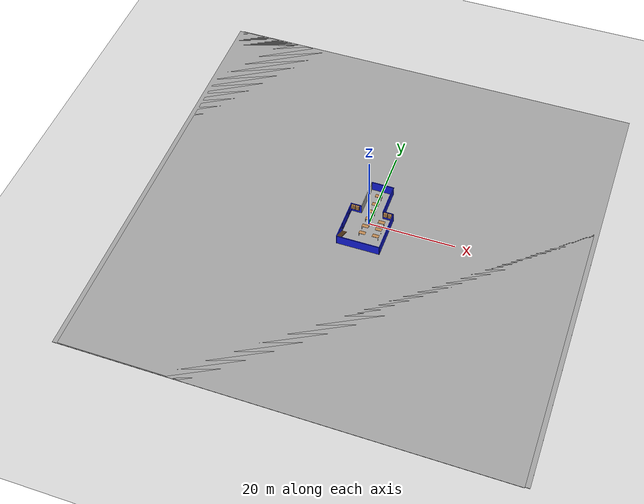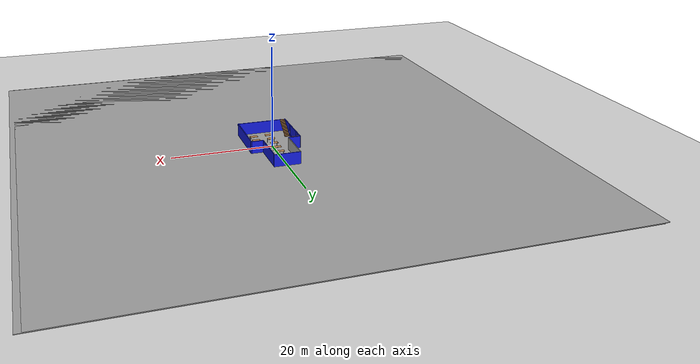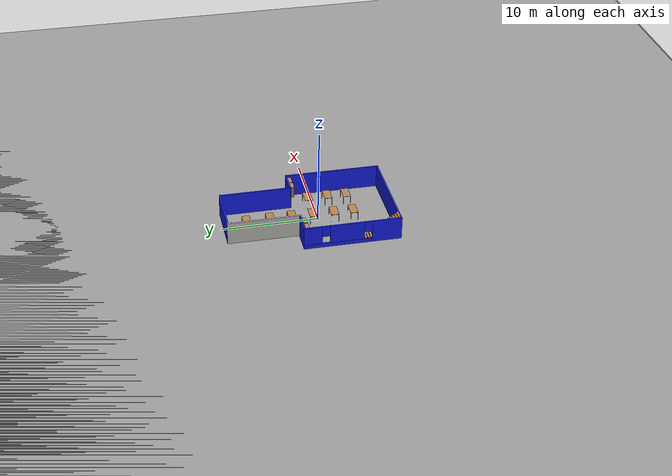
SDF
<sdf version="1.6">
 <world name="default">
  <light name="sun" type="directional">
   <pose>0 0 10 0 -0 0</pose>
   <diffuse>0.8 0.8 0.8 1</diffuse>
   <specular>0.1 0.1 0.1 1</specular>
   <attenuation>
    <range>1000</range>
    <constant>0.9</constant>
    <linear>0.01</linear>
    <quadratic>0.001</quadratic>
   </attenuation>
   <direction>-0.5 0.5 -1</direction>
  </light>
  <model name="ground_plane">
   <static>1</static>
   <link name="link">
    <collision name="collision">
     <geometry><plane><normal>0 0 1</normal><size>100 100</size></plane></geometry>
     <surface><friction><ode><mu>100</mu><mu2>50</mu2></ode></friction></surface>
    </collision>
    <visual name="visual">
     <cast_shadows>0</cast_shadows>
     <geometry><plane><normal>0 0 1</normal><size>100 100</size></plane></geometry>
     <material>
      <script><uri>file://media/materials/scripts/gazebo.material</uri><name>Gazebo/Grey</name></script>
     </material>
    </visual>
   </link>
  </model>
  <gravity>0 0 -9.8</gravity>
  <magnetic_field>6e-06 2.3e-05 -4.2e-05</magnetic_field>
  <atmosphere type="adiabatic"/>
  <physics name="default_physics" default="0" type="ode">
   <max_step_size>0.001</max_step_size>
   <real_time_factor>1</real_time_factor>
   <real_time_update_rate>1000</real_time_update_rate>
  </physics>
  <scene><ambient>0.4 0.4 0.4 1</ambient><background>0.7 0.7 0.7 1</background><shadows>1</shadows></scene>
  <spherical_coordinates>
   <surface_model>EARTH_WGS84</surface_model>
   <latitude_deg>0</latitude_deg>
   <longitude_deg>0</longitude_deg>
   <elevation>0</elevation>
   <heading_deg>0</heading_deg>
  </spherical_coordinates>
  <model name="mySecondHouse_0">
   <link name="Stairs_0">
    <pose>-1.20208 -6.23735 0 0 -0 0</pose>
    <visual name="Stairs_0_Visual_0">
     <pose>-3.16225 4.7318 0.083333 0 -0 0</pose>
     <geometry><box><size>1 0.233333 0.166667</size></box></geometry>
     <material>
      <script><uri>file://media/materials/scripts/gazebo.material</uri><name>Gazebo/Wood</name></script>
      <ambient>1 1 1 1</ambient>
      <diffuse>1 1 1 1</diffuse>
      <specular>0.2 0.2 0.2 1</specular>
      <emissive>0 0 0 1</emissive>
     </material>
    </visual>
    <visual name="Stairs_0_Visual_1">
     <pose>-3.16225 4.49846 0.25 0 -0 0</pose>
     <geometry><box><size>1 0.233333 0.166667</size></box></geometry>
     <material>
      <script><uri>file://media/materials/scripts/gazebo.material</uri><name>Gazebo/Wood</name></script>
      <ambient>1 1 1 1</ambient>
      <diffuse>1 1 1 1</diffuse>
      <specular>0.2 0.2 0.2 1</specular>
      <emissive>0 0 0 1</emissive>
     </material>
    </visual>
    <visual name="Stairs_0_Visual_2">
     <pose>-3.16225 4.26513 0.416667 0 -0 0</pose>
     <geometry><box><size>1 0.233333 0.166667</size></box></geometry>
     <material>
      <script><uri>file://media/materials/scripts/gazebo.material</uri><name>Gazebo/Wood</name></script>
      <ambient>1 1 1 1</ambient>
      <diffuse>1 1 1 1</diffuse>
      <specular>0.2 0.2 0.2 1</specular>
      <emissive>0 0 0 1</emissive>
     </material>
    </visual>
    <visual name="Stairs_0_Visual_3">
     <pose>-3.16225 4.0318 0.583333 0 -0 0</pose>
     <geometry><box><size>1 0.233333 0.166667</size></box></geometry>
     <material>
      <script><uri>file://media/materials/scripts/gazebo.material</uri><name>Gazebo/Wood</name></script>
      <ambient>1 1 1 1</ambient>
      <diffuse>1 1 1 1</diffuse>
      <specular>0.2 0.2 0.2 1</specular>
      <emissive>0 0 0 1</emissive>
     </material>
    </visual>
    <visual name="Stairs_0_Visual_4">
     <pose>-3.16225 3.79846 0.75 0 -0 0</pose>
     <geometry><box><size>1 0.233333 0.166667</size></box></geometry>
     <material>
      <script><uri>file://media/materials/scripts/gazebo.material</uri><name>Gazebo/Wood</name></script>
      <ambient>1 1 1 1</ambient>
      <diffuse>1 1 1 1</diffuse>
      <specular>0.2 0.2 0.2 1</specular>
      <emissive>0 0 0 1</emissive>
     </material>
    </visual>
    <visual name="Stairs_0_Visual_5">
     <pose>-3.16225 3.56513 0.916667 0 -0 0</pose>
     <geometry><box><size>1 0.233333 0.166667</size></box></geometry>
     <material>
      <script><uri>file://media/materials/scripts/gazebo.material</uri><name>Gazebo/Wood</name></script>
      <ambient>1 1 1 1</ambient>
      <diffuse>1 1 1 1</diffuse>
      <specular>0.2 0.2 0.2 1</specular>
      <emissive>0 0 0 1</emissive>
     </material>
    </visual>
    <visual name="Stairs_0_Visual_6">
     <pose>-3.16225 3.3318 1.08333 0 -0 0</pose>
     <geometry><box><size>1 0.233333 0.166667</size></box></geometry>
     <material>
      <script><uri>file://media/materials/scripts/gazebo.material</uri><name>Gazebo/Wood</name></script>
      <ambient>1 1 1 1</ambient>
      <diffuse>1 1 1 1</diffuse>
      <specular>0.2 0.2 0.2 1</specular>
      <emissive>0 0 0 1</emissive>
     </material>
    </visual>
    <visual name="Stairs_0_Visual_7">
     <pose>-3.16225 3.09846 1.25 0 -0 0</pose>
     <geometry><box><size>1 0.233333 0.166667</size></box></geometry>
     <material>
      <script><uri>file://media/materials/scripts/gazebo.material</uri><name>Gazebo/Wood</name></script>
      <ambient>1 1 1 1</ambient>
      <diffuse>1 1 1 1</diffuse>
      <specular>0.2 0.2 0.2 1</specular>
      <emissive>0 0 0 1</emissive>
     </material>
    </visual>
    <visual name="Stairs_0_Visual_8">
     <pose>-3.16225 2.86513 1.41667 0 -0 0</pose>
     <geometry><box><size>1 0.233333 0.166667</size></box></geometry>
     <material>
      <script><uri>file://media/materials/scripts/gazebo.material</uri><name>Gazebo/Wood</name></script>
      <ambient>1 1 1 1</ambient>
      <diffuse>1 1 1 1</diffuse>
      <specular>0.2 0.2 0.2 1</specular>
      <emissive>0 0 0 1</emissive>
     </material>
    </visual>
    <visual name="Stairs_0_Visual_9">
     <pose>-3.16225 2.6318 1.58333 0 -0 0</pose>
     <geometry><box><size>1 0.233333 0.166667</size></box></geometry>
     <material>
      <script><uri>file://media/materials/scripts/gazebo.material</uri><name>Gazebo/Wood</name></script>
      <ambient>1 1 1 1</ambient>
      <diffuse>1 1 1 1</diffuse>
      <specular>0.2 0.2 0.2 1</specular>
      <emissive>0 0 0 1</emissive>
     </material>
    </visual>
    <visual name="Stairs_0_Visual_10">
     <pose>-3.16225 2.39846 1.75 0 -0 0</pose>
     <geometry><box><size>1 0.233333 0.166667</size></box></geometry>
     <material>
      <script><uri>file://media/materials/scripts/gazebo.material</uri><name>Gazebo/Wood</name></script>
      <ambient>1 1 1 1</ambient>
      <diffuse>1 1 1 1</diffuse>
      <specular>0.2 0.2 0.2 1</specular>
      <emissive>0 0 0 1</emissive>
     </material>
    </visual>
    <visual name="Stairs_0_Visual_11">
     <pose>-3.16225 2.16513 1.91667 0 -0 0</pose>
     <geometry><box><size>1 0.233333 0.166667</size></box></geometry>
     <material>
      <script><uri>file://media/materials/scripts/gazebo.material</uri><name>Gazebo/Wood</name></script>
      <ambient>1 1 1 1</ambient>
      <diffuse>1 1 1 1</diffuse>
      <specular>0.2 0.2 0.2 1</specular>
      <emissive>0 0 0 1</emissive>
     </material>
    </visual>
    <visual name="Stairs_0_Visual_12">
     <pose>-3.16225 1.9318 2.08333 0 -0 0</pose>
     <geometry><box><size>1 0.233333 0.166667</size></box></geometry>
     <material>
      <script><uri>file://media/materials/scripts/gazebo.material</uri><name>Gazebo/Wood</name></script>
      <ambient>1 1 1 1</ambient>
      <diffuse>1 1 1 1</diffuse>
      <specular>0.2 0.2 0.2 1</specular>
      <emissive>0 0 0 1</emissive>
     </material>
    </visual>
    <visual name="Stairs_0_Visual_13">
     <pose>-3.16225 1.69846 2.25 0 -0 0</pose>
     <geometry><box><size>1 0.233333 0.166667</size></box></geometry>
     <material>
      <script><uri>file://media/materials/scripts/gazebo.material</uri><name>Gazebo/Wood</name></script>
      <ambient>1 1 1 1</ambient>
      <diffuse>1 1 1 1</diffuse>
      <specular>0.2 0.2 0.2 1</specular>
      <emissive>0 0 0 1</emissive>
     </material>
    </visual>
    <visual name="Stairs_0_Visual_14">
     <pose>-3.16225 1.46513 2.41667 0 -0 0</pose>
     <geometry><box><size>1 0.233333 0.166667</size></box></geometry>
     <material>
      <script><uri>file://media/materials/scripts/gazebo.material</uri><name>Gazebo/Wood</name></script>
      <ambient>1 1 1 1</ambient>
      <diffuse>1 1 1 1</diffuse>
      <specular>0.2 0.2 0.2 1</specular>
      <emissive>0 0 0 1</emissive>
     </material>
    </visual>
    <collision name="Stairs_0_Collision_14">
     <pose>-3.16225 1.46513 2.41667 0 -0 0</pose>
     <geometry><box><size>1 0.233333 0.166667</size></box></geometry>
     <surface>
      <friction>
       <ode><mu>1</mu><mu2>1</mu2><fdir1>0 0 0</fdir1><slip1>0</slip1><slip2>0</slip2></ode>
       <torsional>
        <coefficient>1</coefficient>
        <patch_radius>0</patch_radius>
        <surface_radius>0</surface_radius>
        <use_patch_radius>1</use_patch_radius>
        <ode><slip>0</slip></ode>
       </torsional>
      </friction>
      <bounce><restitution_coefficient>0</restitution_coefficient><threshold>1e+06</threshold></bounce>
      <contact>
       <collide_without_contact>0</collide_without_contact>
       <collide_without_contact_bitmask>1</collide_without_contact_bitmask>
       <collide_bitmask>1</collide_bitmask>
       <ode>
        <soft_cfm>0</soft_cfm>
        <soft_erp>0.2</soft_erp>
        <kp>1e+13</kp>
        <kd>1</kd>
        <max_vel>0.01</max_vel>
        <min_depth>0</min_depth>
       </ode>
       <bullet>
        <split_impulse>1</split_impulse>
        <split_impulse_penetration_threshold>-0.01</split_impulse_penetration_threshold>
        <soft_cfm>0</soft_cfm>
        <soft_erp>0.2</soft_erp>
        <kp>1e+13</kp>
        <kd>1</kd>
       </bullet>
      </contact>
     </surface>
    </collision>
    <collision name="Stairs_0_Collision_0">
     <pose>-3.16225 4.7318 0.083333 0 -0 0</pose>
     <geometry><box><size>1 0.233333 0.166667</size></box></geometry>
     <surface>
      <friction>
       <ode><mu>1</mu><mu2>1</mu2><fdir1>0 0 0</fdir1><slip1>0</slip1><slip2>0</slip2></ode>
       <torsional>
        <coefficient>1</coefficient>
        <patch_radius>0</patch_radius>
        <surface_radius>0</surface_radius>
        <use_patch_radius>1</use_patch_radius>
        <ode><slip>0</slip></ode>
       </torsional>
      </friction>
      <bounce><restitution_coefficient>0</restitution_coefficient><threshold>1e+06</threshold></bounce>
      <contact>
       <collide_without_contact>0</collide_without_contact>
       <collide_without_contact_bitmask>1</collide_without_contact_bitmask>
       <collide_bitmask>1</collide_bitmask>
       <ode>
        <soft_cfm>0</soft_cfm>
        <soft_erp>0.2</soft_erp>
        <kp>1e+13</kp>
        <kd>1</kd>
        <max_vel>0.01</max_vel>
        <min_depth>0</min_depth>
       </ode>
       <bullet>
        <split_impulse>1</split_impulse>
        <split_impulse_penetration_threshold>-0.01</split_impulse_penetration_threshold>
        <soft_cfm>0</soft_cfm>
        <soft_erp>0.2</soft_erp>
        <kp>1e+13</kp>
        <kd>1</kd>
       </bullet>
      </contact>
     </surface>
    </collision>
    <collision name="Stairs_0_Collision_1">
     <pose>-3.16225 4.49846 0.25 0 -0 0</pose>
     <geometry><box><size>1 0.233333 0.166667</size></box></geometry>
     <surface>
      <friction>
       <ode><mu>1</mu><mu2>1</mu2><fdir1>0 0 0</fdir1><slip1>0</slip1><slip2>0</slip2></ode>
       <torsional>
        <coefficient>1</coefficient>
        <patch_radius>0</patch_radius>
        <surface_radius>0</surface_radius>
        <use_patch_radius>1</use_patch_radius>
        <ode><slip>0</slip></ode>
       </torsional>
      </friction>
      <bounce><restitution_coefficient>0</restitution_coefficient><threshold>1e+06</threshold></bounce>
      <contact>
       <collide_without_contact>0</collide_without_contact>
       <collide_without_contact_bitmask>1</collide_without_contact_bitmask>
       <collide_bitmask>1</collide_bitmask>
       <ode>
        <soft_cfm>0</soft_cfm>
        <soft_erp>0.2</soft_erp>
        <kp>1e+13</kp>
        <kd>1</kd>
        <max_vel>0.01</max_vel>
        <min_depth>0</min_depth>
       </ode>
       <bullet>
        <split_impulse>1</split_impulse>
        <split_impulse_penetration_threshold>-0.01</split_impulse_penetration_threshold>
        <soft_cfm>0</soft_cfm>
        <soft_erp>0.2</soft_erp>
        <kp>1e+13</kp>
        <kd>1</kd>
       </bullet>
      </contact>
     </surface>
    </collision>
    <collision name="Stairs_0_Collision_2">
     <pose>-3.16225 4.26513 0.416667 0 -0 0</pose>
     <geometry><box><size>1 0.233333 0.166667</size></box></geometry>
     <surface>
      <friction>
       <ode><mu>1</mu><mu2>1</mu2><fdir1>0 0 0</fdir1><slip1>0</slip1><slip2>0</slip2></ode>
       <torsional>
        <coefficient>1</coefficient>
        <patch_radius>0</patch_radius>
        <surface_radius>0</surface_radius>
        <use_patch_radius>1</use_patch_radius>
        <ode><slip>0</slip></ode>
       </torsional>
      </friction>
      <bounce><restitution_coefficient>0</restitution_coefficient><threshold>1e+06</threshold></bounce>
      <contact>
       <collide_without_contact>0</collide_without_contact>
       <collide_without_contact_bitmask>1</collide_without_contact_bitmask>
       <collide_bitmask>1</collide_bitmask>
       <ode>
        <soft_cfm>0</soft_cfm>
        <soft_erp>0.2</soft_erp>
        <kp>1e+13</kp>
        <kd>1</kd>
        <max_vel>0.01</max_vel>
        <min_depth>0</min_depth>
       </ode>
       <bullet>
        <split_impulse>1</split_impulse>
        <split_impulse_penetration_threshold>-0.01</split_impulse_penetration_threshold>
        <soft_cfm>0</soft_cfm>
        <soft_erp>0.2</soft_erp>
        <kp>1e+13</kp>
        <kd>1</kd>
       </bullet>
      </contact>
     </surface>
    </collision>
    <collision name="Stairs_0_Collision_3">
     <pose>-3.16225 4.0318 0.583333 0 -0 0</pose>
     <geometry><box><size>1 0.233333 0.166667</size></box></geometry>
     <surface>
      <friction>
       <ode><mu>1</mu><mu2>1</mu2><fdir1>0 0 0</fdir1><slip1>0</slip1><slip2>0</slip2></ode>
       <torsional>
        <coefficient>1</coefficient>
        <patch_radius>0</patch_radius>
        <surface_radius>0</surface_radius>
        <use_patch_radius>1</use_patch_radius>
        <ode><slip>0</slip></ode>
       </torsional>
      </friction>
      <bounce><restitution_coefficient>0</restitution_coefficient><threshold>1e+06</threshold></bounce>
      <contact>
       <collide_without_contact>0</collide_without_contact>
       <collide_without_contact_bitmask>1</collide_without_contact_bitmask>
       <collide_bitmask>1</collide_bitmask>
       <ode>
        <soft_cfm>0</soft_cfm>
        <soft_erp>0.2</soft_erp>
        <kp>1e+13</kp>
        <kd>1</kd>
        <max_vel>0.01</max_vel>
        <min_depth>0</min_depth>
       </ode>
       <bullet>
        <split_impulse>1</split_impulse>
        <split_impulse_penetration_threshold>-0.01</split_impulse_penetration_threshold>
        <soft_cfm>0</soft_cfm>
        <soft_erp>0.2</soft_erp>
        <kp>1e+13</kp>
        <kd>1</kd>
       </bullet>
      </contact>
     </surface>
    </collision>
    <collision name="Stairs_0_Collision_5">
     <pose>-3.16225 3.56513 0.916667 0 -0 0</pose>
     <geometry><box><size>1 0.233333 0.166667</size></box></geometry>
     <surface>
      <friction>
       <ode><mu>1</mu><mu2>1</mu2><fdir1>0 0 0</fdir1><slip1>0</slip1><slip2>0</slip2></ode>
       <torsional>
        <coefficient>1</coefficient>
        <patch_radius>0</patch_radius>
        <surface_radius>0</surface_radius>
        <use_patch_radius>1</use_patch_radius>
        <ode><slip>0</slip></ode>
       </torsional>
      </friction>
      <bounce><restitution_coefficient>0</restitution_coefficient><threshold>1e+06</threshold></bounce>
      <contact>
       <collide_without_contact>0</collide_without_contact>
       <collide_without_contact_bitmask>1</collide_without_contact_bitmask>
       <collide_bitmask>1</collide_bitmask>
       <ode>
        <soft_cfm>0</soft_cfm>
        <soft_erp>0.2</soft_erp>
        <kp>1e+13</kp>
        <kd>1</kd>
        <max_vel>0.01</max_vel>
        <min_depth>0</min_depth>
       </ode>
       <bullet>
        <split_impulse>1</split_impulse>
        <split_impulse_penetration_threshold>-0.01</split_impulse_penetration_threshold>
        <soft_cfm>0</soft_cfm>
        <soft_erp>0.2</soft_erp>
        <kp>1e+13</kp>
        <kd>1</kd>
       </bullet>
      </contact>
     </surface>
    </collision>
    <collision name="Stairs_0_Collision_6">
     <pose>-3.16225 3.3318 1.08333 0 -0 0</pose>
     <geometry><box><size>1 0.233333 0.166667</size></box></geometry>
     <surface>
      <friction>
       <ode><mu>1</mu><mu2>1</mu2><fdir1>0 0 0</fdir1><slip1>0</slip1><slip2>0</slip2></ode>
       <torsional>
        <coefficient>1</coefficient>
        <patch_radius>0</patch_radius>
        <surface_radius>0</surface_radius>
        <use_patch_radius>1</use_patch_radius>
        <ode><slip>0</slip></ode>
       </torsional>
      </friction>
      <bounce><restitution_coefficient>0</restitution_coefficient><threshold>1e+06</threshold></bounce>
      <contact>
       <collide_without_contact>0</collide_without_contact>
       <collide_without_contact_bitmask>1</collide_without_contact_bitmask>
       <collide_bitmask>1</collide_bitmask>
       <ode>
        <soft_cfm>0</soft_cfm>
        <soft_erp>0.2</soft_erp>
        <kp>1e+13</kp>
        <kd>1</kd>
        <max_vel>0.01</max_vel>
        <min_depth>0</min_depth>
       </ode>
       <bullet>
        <split_impulse>1</split_impulse>
        <split_impulse_penetration_threshold>-0.01</split_impulse_penetration_threshold>
        <soft_cfm>0</soft_cfm>
        <soft_erp>0.2</soft_erp>
        <kp>1e+13</kp>
        <kd>1</kd>
       </bullet>
      </contact>
     </surface>
    </collision>
    <collision name="Stairs_0_Collision_4">
     <pose>-3.16225 3.79846 0.75 0 -0 0</pose>
     <geometry><box><size>1 0.233333 0.166667</size></box></geometry>
     <surface>
      <friction>
       <ode><mu>1</mu><mu2>1</mu2><fdir1>0 0 0</fdir1><slip1>0</slip1><slip2>0</slip2></ode>
       <torsional>
        <coefficient>1</coefficient>
        <patch_radius>0</patch_radius>
        <surface_radius>0</surface_radius>
        <use_patch_radius>1</use_patch_radius>
        <ode><slip>0</slip></ode>
       </torsional>
      </friction>
      <bounce><restitution_coefficient>0</restitution_coefficient><threshold>1e+06</threshold></bounce>
      <contact>
       <collide_without_contact>0</collide_without_contact>
       <collide_without_contact_bitmask>1</collide_without_contact_bitmask>
       <collide_bitmask>1</collide_bitmask>
       <ode>
        <soft_cfm>0</soft_cfm>
        <soft_erp>0.2</soft_erp>
        <kp>1e+13</kp>
        <kd>1</kd>
        <max_vel>0.01</max_vel>
        <min_depth>0</min_depth>
       </ode>
       <bullet>
        <split_impulse>1</split_impulse>
        <split_impulse_penetration_threshold>-0.01</split_impulse_penetration_threshold>
        <soft_cfm>0</soft_cfm>
        <soft_erp>0.2</soft_erp>
        <kp>1e+13</kp>
        <kd>1</kd>
       </bullet>
      </contact>
     </surface>
    </collision>
    <collision name="Stairs_0_Collision_9">
     <pose>-3.16225 2.6318 1.58333 0 -0 0</pose>
     <geometry><box><size>1 0.233333 0.166667</size></box></geometry>
     <surface>
      <friction>
       <ode><mu>1</mu><mu2>1</mu2><fdir1>0 0 0</fdir1><slip1>0</slip1><slip2>0</slip2></ode>
       <torsional>
        <coefficient>1</coefficient>
        <patch_radius>0</patch_radius>
        <surface_radius>0</surface_radius>
        <use_patch_radius>1</use_patch_radius>
        <ode><slip>0</slip></ode>
       </torsional>
      </friction>
      <bounce><restitution_coefficient>0</restitution_coefficient><threshold>1e+06</threshold></bounce>
      <contact>
       <collide_without_contact>0</collide_without_contact>
       <collide_without_contact_bitmask>1</collide_without_contact_bitmask>
       <collide_bitmask>1</collide_bitmask>
       <ode>
        <soft_cfm>0</soft_cfm>
        <soft_erp>0.2</soft_erp>
        <kp>1e+13</kp>
        <kd>1</kd>
        <max_vel>0.01</max_vel>
        <min_depth>0</min_depth>
       </ode>
       <bullet>
        <split_impulse>1</split_impulse>
        <split_impulse_penetration_threshold>-0.01</split_impulse_penetration_threshold>
        <soft_cfm>0</soft_cfm>
        <soft_erp>0.2</soft_erp>
        <kp>1e+13</kp>
        <kd>1</kd>
       </bullet>
      </contact>
     </surface>
    </collision>
    <collision name="Stairs_0_Collision_7">
     <pose>-3.16225 3.09846 1.25 0 -0 0</pose>
     <geometry><box><size>1 0.233333 0.166667</size></box></geometry>
     <surface>
      <friction>
       <ode><mu>1</mu><mu2>1</mu2><fdir1>0 0 0</fdir1><slip1>0</slip1><slip2>0</slip2></ode>
       <torsional>
        <coefficient>1</coefficient>
        <patch_radius>0</patch_radius>
        <surface_radius>0</surface_radius>
        <use_patch_radius>1</use_patch_radius>
        <ode><slip>0</slip></ode>
       </torsional>
      </friction>
      <bounce><restitution_coefficient>0</restitution_coefficient><threshold>1e+06</threshold></bounce>
      <contact>
       <collide_without_contact>0</collide_without_contact>
       <collide_without_contact_bitmask>1</collide_without_contact_bitmask>
       <collide_bitmask>1</collide_bitmask>
       <ode>
        <soft_cfm>0</soft_cfm>
        <soft_erp>0.2</soft_erp>
        <kp>1e+13</kp>
        <kd>1</kd>
        <max_vel>0.01</max_vel>
        <min_depth>0</min_depth>
       </ode>
       <bullet>
        <split_impulse>1</split_impulse>
        <split_impulse_penetration_threshold>-0.01</split_impulse_penetration_threshold>
        <soft_cfm>0</soft_cfm>
        <soft_erp>0.2</soft_erp>
        <kp>1e+13</kp>
        <kd>1</kd>
       </bullet>
      </contact>
     </surface>
    </collision>
    <collision name="Stairs_0_Collision_8">
     <pose>-3.16225 2.86513 1.41667 0 -0 0</pose>
     <geometry><box><size>1 0.233333 0.166667</size></box></geometry>
     <surface>
      <friction>
       <ode><mu>1</mu><mu2>1</mu2><fdir1>0 0 0</fdir1><slip1>0</slip1><slip2>0</slip2></ode>
       <torsional>
        <coefficient>1</coefficient>
        <patch_radius>0</patch_radius>
        <surface_radius>0</surface_radius>
        <use_patch_radius>1</use_patch_radius>
        <ode><slip>0</slip></ode>
       </torsional>
      </friction>
      <bounce><restitution_coefficient>0</restitution_coefficient><threshold>1e+06</threshold></bounce>
      <contact>
       <collide_without_contact>0</collide_without_contact>
       <collide_without_contact_bitmask>1</collide_without_contact_bitmask>
       <collide_bitmask>1</collide_bitmask>
       <ode>
        <soft_cfm>0</soft_cfm>
        <soft_erp>0.2</soft_erp>
        <kp>1e+13</kp>
        <kd>1</kd>
        <max_vel>0.01</max_vel>
        <min_depth>0</min_depth>
       </ode>
       <bullet>
        <split_impulse>1</split_impulse>
        <split_impulse_penetration_threshold>-0.01</split_impulse_penetration_threshold>
        <soft_cfm>0</soft_cfm>
        <soft_erp>0.2</soft_erp>
        <kp>1e+13</kp>
        <kd>1</kd>
       </bullet>
      </contact>
     </surface>
    </collision>
    <collision name="Stairs_0_Collision_10">
     <pose>-3.16225 2.39846 1.75 0 -0 0</pose>
     <geometry><box><size>1 0.233333 0.166667</size></box></geometry>
     <surface>
      <friction>
       <ode><mu>1</mu><mu2>1</mu2><fdir1>0 0 0</fdir1><slip1>0</slip1><slip2>0</slip2></ode>
       <torsional>
        <coefficient>1</coefficient>
        <patch_radius>0</patch_radius>
        <surface_radius>0</surface_radius>
        <use_patch_radius>1</use_patch_radius>
        <ode><slip>0</slip></ode>
       </torsional>
      </friction>
      <bounce><restitution_coefficient>0</restitution_coefficient><threshold>1e+06</threshold></bounce>
      <contact>
       <collide_without_contact>0</collide_without_contact>
       <collide_without_contact_bitmask>1</collide_without_contact_bitmask>
       <collide_bitmask>1</collide_bitmask>
       <ode>
        <soft_cfm>0</soft_cfm>
        <soft_erp>0.2</soft_erp>
        <kp>1e+13</kp>
        <kd>1</kd>
        <max_vel>0.01</max_vel>
        <min_depth>0</min_depth>
       </ode>
       <bullet>
        <split_impulse>1</split_impulse>
        <split_impulse_penetration_threshold>-0.01</split_impulse_penetration_threshold>
        <soft_cfm>0</soft_cfm>
        <soft_erp>0.2</soft_erp>
        <kp>1e+13</kp>
        <kd>1</kd>
       </bullet>
      </contact>
     </surface>
    </collision>
    <collision name="Stairs_0_Collision_11">
     <pose>-3.16225 2.16513 1.91667 0 -0 0</pose>
     <geometry><box><size>1 0.233333 0.166667</size></box></geometry>
     <surface>
      <friction>
       <ode><mu>1</mu><mu2>1</mu2><fdir1>0 0 0</fdir1><slip1>0</slip1><slip2>0</slip2></ode>
       <torsional>
        <coefficient>1</coefficient>
        <patch_radius>0</patch_radius>
        <surface_radius>0</surface_radius>
        <use_patch_radius>1</use_patch_radius>
        <ode><slip>0</slip></ode>
       </torsional>
      </friction>
      <bounce><restitution_coefficient>0</restitution_coefficient><threshold>1e+06</threshold></bounce>
      <contact>
       <collide_without_contact>0</collide_without_contact>
       <collide_without_contact_bitmask>1</collide_without_contact_bitmask>
       <collide_bitmask>1</collide_bitmask>
       <ode>
        <soft_cfm>0</soft_cfm>
        <soft_erp>0.2</soft_erp>
        <kp>1e+13</kp>
        <kd>1</kd>
        <max_vel>0.01</max_vel>
        <min_depth>0</min_depth>
       </ode>
       <bullet>
        <split_impulse>1</split_impulse>
        <split_impulse_penetration_threshold>-0.01</split_impulse_penetration_threshold>
        <soft_cfm>0</soft_cfm>
        <soft_erp>0.2</soft_erp>
        <kp>1e+13</kp>
        <kd>1</kd>
       </bullet>
      </contact>
     </surface>
    </collision>
    <collision name="Stairs_0_Collision_12">
     <pose>-3.16225 1.9318 2.08333 0 -0 0</pose>
     <geometry><box><size>1 0.233333 0.166667</size></box></geometry>
     <surface>
      <friction>
       <ode><mu>1</mu><mu2>1</mu2><fdir1>0 0 0</fdir1><slip1>0</slip1><slip2>0</slip2></ode>
       <torsional>
        <coefficient>1</coefficient>
        <patch_radius>0</patch_radius>
        <surface_radius>0</surface_radius>
        <use_patch_radius>1</use_patch_radius>
        <ode><slip>0</slip></ode>
       </torsional>
      </friction>
      <bounce><restitution_coefficient>0</restitution_coefficient><threshold>1e+06</threshold></bounce>
      <contact>
       <collide_without_contact>0</collide_without_contact>
       <collide_without_contact_bitmask>1</collide_without_contact_bitmask>
       <collide_bitmask>1</collide_bitmask>
       <ode>
        <soft_cfm>0</soft_cfm>
        <soft_erp>0.2</soft_erp>
        <kp>1e+13</kp>
        <kd>1</kd>
        <max_vel>0.01</max_vel>
        <min_depth>0</min_depth>
       </ode>
       <bullet>
        <split_impulse>1</split_impulse>
        <split_impulse_penetration_threshold>-0.01</split_impulse_penetration_threshold>
        <soft_cfm>0</soft_cfm>
        <soft_erp>0.2</soft_erp>
        <kp>1e+13</kp>
        <kd>1</kd>
       </bullet>
      </contact>
     </surface>
    </collision>
    <collision name="Stairs_0_Collision_13">
     <pose>-3.16225 1.69846 2.25 0 -0 0</pose>
     <geometry><box><size>1 0.233333 0.166667</size></box></geometry>
     <surface>
      <friction>
       <ode><mu>1</mu><mu2>1</mu2><fdir1>0 0 0</fdir1><slip1>0</slip1><slip2>0</slip2></ode>
       <torsional>
        <coefficient>1</coefficient>
        <patch_radius>0</patch_radius>
        <surface_radius>0</surface_radius>
        <use_patch_radius>1</use_patch_radius>
        <ode><slip>0</slip></ode>
       </torsional>
      </friction>
      <bounce><restitution_coefficient>0</restitution_coefficient><threshold>1e+06</threshold></bounce>
      <contact>
       <collide_without_contact>0</collide_without_contact>
       <collide_without_contact_bitmask>1</collide_without_contact_bitmask>
       <collide_bitmask>1</collide_bitmask>
       <ode>
        <soft_cfm>0</soft_cfm>
        <soft_erp>0.2</soft_erp>
        <kp>1e+13</kp>
        <kd>1</kd>
        <max_vel>0.01</max_vel>
        <min_depth>0</min_depth>
       </ode>
       <bullet>
        <split_impulse>1</split_impulse>
        <split_impulse_penetration_threshold>-0.01</split_impulse_penetration_threshold>
        <soft_cfm>0</soft_cfm>
        <soft_erp>0.2</soft_erp>
        <kp>1e+13</kp>
        <kd>1</kd>
       </bullet>
      </contact>
     </surface>
    </collision>
   </link>
   <link name="Wall_26">
    <pose>-3.71974 4.925 0 0 -0 0</pose>
    <visual name="Wall_26_Visual">
     <pose>0 0 1.25 0 -0 0</pose>
     <geometry><box><size>2.5 0.15 2.5</size></box></geometry>
     <material>
      <script><uri>file://media/materials/scripts/gazebo.material</uri><name>Gazebo/Grey</name></script>
      <ambient>0.0980392 0.141176 1 1</ambient>
      <diffuse>0.7 0.7 0.7 1</diffuse>
      <specular>0.01 0.01 0.01 1</specular>
      <emissive>0 0 0 1</emissive>
     </material>
    </visual>
    <collision name="Wall_26_Collision">
     <pose>0 0 1.25 0 -0 0</pose>
     <geometry><box><size>2.5 0.15 2.5</size></box></geometry>
     <surface>
      <friction>
       <ode><mu>1</mu><mu2>1</mu2><fdir1>0 0 0</fdir1><slip1>0</slip1><slip2>0</slip2></ode>
       <torsional>
        <coefficient>1</coefficient>
        <patch_radius>0</patch_radius>
        <surface_radius>0</surface_radius>
        <use_patch_radius>1</use_patch_radius>
        <ode><slip>0</slip></ode>
       </torsional>
      </friction>
      <bounce><restitution_coefficient>0</restitution_coefficient><threshold>1e+06</threshold></bounce>
      <contact>
       <collide_without_contact>0</collide_without_contact>
       <collide_without_contact_bitmask>1</collide_without_contact_bitmask>
       <collide_bitmask>1</collide_bitmask>
       <ode>
        <soft_cfm>0</soft_cfm>
        <soft_erp>0.2</soft_erp>
        <kp>1e+13</kp>
        <kd>1</kd>
        <max_vel>0.01</max_vel>
        <min_depth>0</min_depth>
       </ode>
       <bullet>
        <split_impulse>1</split_impulse>
        <split_impulse_penetration_threshold>-0.01</split_impulse_penetration_threshold>
        <soft_cfm>0</soft_cfm>
        <soft_erp>0.2</soft_erp>
        <kp>1e+13</kp>
        <kd>1</kd>
       </bullet>
      </contact>
     </surface>
    </collision>
   </link>
   <link name="Wall_27">
    <pose>-2.54213 8.59143 0 0 0 -1.57151</pose>
    <inertial>
     <inertia><ixx>nan</ixx><ixy>0</ixy><ixz>0</ixz><iyy>nan</iyy><iyz>0</iyz><izz>nan</izz></inertia>
     <mass>0</mass>
    </inertial>
    <visual name="Wall_27_Visual">
     <pose>0 0 1.25 0 -0 0</pose>
     <geometry><box><size>7.48003 0.15 2.5</size></box></geometry>
     <material>
      <script><uri>file://media/materials/scripts/gazebo.material</uri><name>Gazebo/CeilingTiled</name></script>
      <ambient>0.0980392 0.141176 1 1</ambient>
      <diffuse>1 1 1 1</diffuse>
      <specular>0 0 0 1</specular>
      <emissive>0 0 0 1</emissive>
     </material>
    </visual>
    <collision name="Wall_27_Collision">
     <pose>0 0 1.25 0 -0 0</pose>
     <geometry><box><size>7.48003 0.15 2.5</size></box></geometry>
     <surface>
      <friction>
       <ode><mu>1</mu><mu2>1</mu2><fdir1>0 0 0</fdir1><slip1>0</slip1><slip2>0</slip2></ode>
       <torsional>
        <coefficient>1</coefficient>
        <patch_radius>0</patch_radius>
        <surface_radius>0</surface_radius>
        <use_patch_radius>1</use_patch_radius>
        <ode><slip>0</slip></ode>
       </torsional>
      </friction>
      <bounce><restitution_coefficient>0</restitution_coefficient><threshold>1e+06</threshold></bounce>
      <contact>
       <collide_without_contact>0</collide_without_contact>
       <collide_without_contact_bitmask>1</collide_without_contact_bitmask>
       <collide_bitmask>1</collide_bitmask>
       <ode>
        <soft_cfm>0</soft_cfm>
        <soft_erp>0.2</soft_erp>
        <kp>1e+13</kp>
        <kd>1</kd>
        <max_vel>0.01</max_vel>
        <min_depth>0</min_depth>
       </ode>
       <bullet>
        <split_impulse>1</split_impulse>
        <split_impulse_penetration_threshold>-0.01</split_impulse_penetration_threshold>
        <soft_cfm>0</soft_cfm>
        <soft_erp>0.2</soft_erp>
        <kp>1e+13</kp>
        <kd>1</kd>
       </bullet>
      </contact>
     </surface>
    </collision>
   </link>
   <link name="Wall_28">
    <pose>0.035567 12.2589 0 0 -0 0</pose>
    <visual name="Wall_28_Visual">
     <pose>0 0 1.25 0 -0 0</pose>
     <geometry><box><size>5.25 0.15 2.5</size></box></geometry>
     <material>
      <script><uri>file://media/materials/scripts/gazebo.material</uri><name>Gazebo/Grey</name></script>
      <ambient>0.0980392 0.141176 1 1</ambient>
      <diffuse>0.7 0.7 0.7 1</diffuse>
      <specular>0.01 0.01 0.01 1</specular>
      <emissive>0 0 0 1</emissive>
     </material>
    </visual>
    <collision name="Wall_28_Collision">
     <pose>0 0 1.25 0 -0 0</pose>
     <geometry><box><size>5.25 0.15 2.5</size></box></geometry>
     <surface>
      <friction>
       <ode><mu>1</mu><mu2>1</mu2><fdir1>0 0 0</fdir1><slip1>0</slip1><slip2>0</slip2></ode>
       <torsional>
        <coefficient>1</coefficient>
        <patch_radius>0</patch_radius>
        <surface_radius>0</surface_radius>
        <use_patch_radius>1</use_patch_radius>
        <ode><slip>0</slip></ode>
       </torsional>
      </friction>
      <bounce><restitution_coefficient>0</restitution_coefficient><threshold>1e+06</threshold></bounce>
      <contact>
       <collide_without_contact>0</collide_without_contact>
       <collide_without_contact_bitmask>1</collide_without_contact_bitmask>
       <collide_bitmask>1</collide_bitmask>
       <ode>
        <soft_cfm>0</soft_cfm>
        <soft_erp>0.2</soft_erp>
        <kp>1e+13</kp>
        <kd>1</kd>
        <max_vel>0.01</max_vel>
        <min_depth>0</min_depth>
       </ode>
       <bullet>
        <split_impulse>1</split_impulse>
        <split_impulse_penetration_threshold>-0.01</split_impulse_penetration_threshold>
        <soft_cfm>0</soft_cfm>
        <soft_erp>0.2</soft_erp>
        <kp>1e+13</kp>
        <kd>1</kd>
       </bullet>
      </contact>
     </surface>
    </collision>
   </link>
   <link name="Wall_29">
    <pose>2.54684 8.53962 0 0 -0 1.57417</pose>
    <inertial>
     <inertia><ixx>nan</ixx><ixy>0</ixy><ixz>0</ixz><iyy>nan</iyy><iyz>0</iyz><izz>nan</izz></inertia>
     <mass>0</mass>
    </inertial>
    <visual name="Wall_29_Visual">
     <pose>0 0 1.25 0 -0 0</pose>
     <geometry><box><size>7.33027 0.15 2.5</size></box></geometry>
     <material>
      <script><uri>file://media/materials/scripts/gazebo.material</uri><name>Gazebo/Grey</name></script>
      <ambient>0.0980392 0.141176 1 1</ambient>
      <diffuse>0.7 0.7 0.7 1</diffuse>
      <specular>0.01 0.01 0.01 1</specular>
      <emissive>0 0 0 1</emissive>
     </material>
    </visual>
    <collision name="Wall_29_Collision">
     <pose>0 0 1.25 0 -0 0</pose>
     <geometry><box><size>7.33027 0.15 2.5</size></box></geometry>
     <surface>
      <friction>
       <ode><mu>1</mu><mu2>1</mu2><fdir1>0 0 0</fdir1><slip1>0</slip1><slip2>0</slip2></ode>
       <torsional>
        <coefficient>1</coefficient>
        <patch_radius>0</patch_radius>
        <surface_radius>0</surface_radius>
        <use_patch_radius>1</use_patch_radius>
        <ode><slip>0</slip></ode>
       </torsional>
      </friction>
      <bounce><restitution_coefficient>0</restitution_coefficient><threshold>1e+06</threshold></bounce>
      <contact>
       <collide_without_contact>0</collide_without_contact>
       <collide_without_contact_bitmask>1</collide_without_contact_bitmask>
       <collide_bitmask>1</collide_bitmask>
       <ode>
        <soft_cfm>0</soft_cfm>
        <soft_erp>0.2</soft_erp>
        <kp>1e+13</kp>
        <kd>1</kd>
        <max_vel>0.01</max_vel>
        <min_depth>0</min_depth>
       </ode>
       <bullet>
        <split_impulse>1</split_impulse>
        <split_impulse_penetration_threshold>-0.01</split_impulse_penetration_threshold>
        <soft_cfm>0</soft_cfm>
        <soft_erp>0.2</soft_erp>
        <kp>1e+13</kp>
        <kd>1</kd>
       </bullet>
      </contact>
     </surface>
    </collision>
   </link>
   <link name="Wall_30">
    <pose>3.77003 4.925 0 0 -0 0</pose>
    <visual name="Wall_30_Visual">
     <pose>0 0 1.25 0 -0 0</pose>
     <geometry><box><size>2.5 0.15 2.5</size></box></geometry>
     <material>
      <script><uri>file://media/materials/scripts/gazebo.material</uri><name>Gazebo/Grey</name></script>
      <ambient>0.0980392 0.141176 1 1</ambient>
      <diffuse>0.7 0.7 0.7 1</diffuse>
      <specular>0.01 0.01 0.01 1</specular>
      <emissive>0 0 0 1</emissive>
     </material>
    </visual>
    <collision name="Wall_30_Collision">
     <pose>0 0 1.25 0 -0 0</pose>
     <geometry><box><size>2.5 0.15 2.5</size></box></geometry>
     <surface>
      <friction>
       <ode><mu>1</mu><mu2>1</mu2><fdir1>0 0 0</fdir1><slip1>0</slip1><slip2>0</slip2></ode>
       <torsional>
        <coefficient>1</coefficient>
        <patch_radius>0</patch_radius>
        <surface_radius>0</surface_radius>
        <use_patch_radius>1</use_patch_radius>
        <ode><slip>0</slip></ode>
       </torsional>
      </friction>
      <bounce><restitution_coefficient>0</restitution_coefficient><threshold>1e+06</threshold></bounce>
      <contact>
       <collide_without_contact>0</collide_without_contact>
       <collide_without_contact_bitmask>1</collide_without_contact_bitmask>
       <collide_bitmask>1</collide_bitmask>
       <ode>
        <soft_cfm>0</soft_cfm>
        <soft_erp>0.2</soft_erp>
        <kp>1e+13</kp>
        <kd>1</kd>
        <max_vel>0.01</max_vel>
        <min_depth>0</min_depth>
       </ode>
       <bullet>
        <split_impulse>1</split_impulse>
        <split_impulse_penetration_threshold>-0.01</split_impulse_penetration_threshold>
        <soft_cfm>0</soft_cfm>
        <soft_erp>0.2</soft_erp>
        <kp>1e+13</kp>
        <kd>1</kd>
       </bullet>
      </contact>
     </surface>
    </collision>
   </link>
   <link name="Wall_31">
    <pose>4.90715 0 0 0 0 -1.57118</pose>
    <visual name="Wall_31_Visual">
     <pose>0 0 1.25 0 -0 0</pose>
     <geometry><box><size>10.0006 0.15 2.5</size></box></geometry>
     <material>
      <script><uri>file://media/materials/scripts/gazebo.material</uri><name>Gazebo/Grey</name></script>
      <ambient>0.0980392 0.141176 1 1</ambient>
      <diffuse>0.7 0.7 0.7 1</diffuse>
      <specular>0.01 0.01 0.01 1</specular>
      <emissive>0 0 0 1</emissive>
     </material>
    </visual>
    <collision name="Wall_31_Collision">
     <pose>0 0 1.25 0 -0 0</pose>
     <geometry><box><size>10.0006 0.15 2.5</size></box></geometry>
     <surface>
      <friction>
       <ode><mu>1</mu><mu2>1</mu2><fdir1>0 0 0</fdir1><slip1>0</slip1><slip2>0</slip2></ode>
       <torsional>
        <coefficient>1</coefficient>
        <patch_radius>0</patch_radius>
        <surface_radius>0</surface_radius>
        <use_patch_radius>1</use_patch_radius>
        <ode><slip>0</slip></ode>
       </torsional>
      </friction>
      <bounce><restitution_coefficient>0</restitution_coefficient><threshold>1e+06</threshold></bounce>
      <contact>
       <collide_without_contact>0</collide_without_contact>
       <collide_without_contact_bitmask>1</collide_without_contact_bitmask>
       <collide_bitmask>1</collide_bitmask>
       <ode>
        <soft_cfm>0</soft_cfm>
        <soft_erp>0.2</soft_erp>
        <kp>1e+13</kp>
        <kd>1</kd>
        <max_vel>0.01</max_vel>
        <min_depth>0</min_depth>
       </ode>
       <bullet>
        <split_impulse>1</split_impulse>
        <split_impulse_penetration_threshold>-0.01</split_impulse_penetration_threshold>
        <soft_cfm>0</soft_cfm>
        <soft_erp>0.2</soft_erp>
        <kp>1e+13</kp>
        <kd>1</kd>
       </bullet>
      </contact>
     </surface>
    </collision>
   </link>
   <link name="Wall_32">
    <pose>-0.007443 -4.89795 0 0 -0 3.14156</pose>
    <visual name="Wall_32_Visual">
     <pose>0 0 1.25 0 -0 0</pose>
     <geometry><box><size>10 0.15 2.5</size></box></geometry>
     <material>
      <script><uri>file://media/materials/scripts/gazebo.material</uri><name>Gazebo/Grey</name></script>
      <ambient>0.0980392 0.141176 1 1</ambient>
      <diffuse>0.7 0.7 0.7 1</diffuse>
      <specular>0.01 0.01 0.01 1</specular>
      <emissive>0 0 0 1</emissive>
     </material>
    </visual>
    <collision name="Wall_32_Collision">
     <pose>0 0 1.25 0 -0 0</pose>
     <geometry><box><size>10 0.15 2.5</size></box></geometry>
     <surface>
      <friction>
       <ode><mu>1</mu><mu2>1</mu2><fdir1>0 0 0</fdir1><slip1>0</slip1><slip2>0</slip2></ode>
       <torsional>
        <coefficient>1</coefficient>
        <patch_radius>0</patch_radius>
        <surface_radius>0</surface_radius>
        <use_patch_radius>1</use_patch_radius>
        <ode><slip>0</slip></ode>
       </torsional>
      </friction>
      <bounce><restitution_coefficient>0</restitution_coefficient><threshold>1e+06</threshold></bounce>
      <contact>
       <collide_without_contact>0</collide_without_contact>
       <collide_without_contact_bitmask>1</collide_without_contact_bitmask>
       <collide_bitmask>1</collide_bitmask>
       <ode>
        <soft_cfm>0</soft_cfm>
        <soft_erp>0.2</soft_erp>
        <kp>1e+13</kp>
        <kd>1</kd>
        <max_vel>0.01</max_vel>
        <min_depth>0</min_depth>
       </ode>
       <bullet>
        <split_impulse>1</split_impulse>
        <split_impulse_penetration_threshold>-0.01</split_impulse_penetration_threshold>
        <soft_cfm>0</soft_cfm>
        <soft_erp>0.2</soft_erp>
        <kp>1e+13</kp>
        <kd>1</kd>
       </bullet>
      </contact>
     </surface>
    </collision>
   </link>
   <link name="Wall_33">
    <pose>-4.94503 0.000313 0 0 -0 1.5708</pose>
    <visual name="Wall_33_Visual_0">
     <pose>-3.48148 0 1.25 0 -0 0</pose>
     <geometry><box><size>3.03703 0.15 2.5</size></box></geometry>
     <material>
      <script><uri>file://media/materials/scripts/gazebo.material</uri><name>Gazebo/Grey</name></script>
      <ambient>0.0980392 0.141176 1 1</ambient>
      <diffuse>0.7 0.7 0.7 1</diffuse>
      <specular>0.01 0.01 0.01 1</specular>
      <emissive>0 0 0 1</emissive>
     </material>
    </visual>
    <visual name="Wall_33_Visual_1">
     <pose>1.51852 0 0.25 0 -0 0</pose>
     <geometry><box><size>6.96297 0.15 0.5</size></box></geometry>
     <material>
      <script><uri>file://media/materials/scripts/gazebo.material</uri><name>Gazebo/Grey</name></script>
      <ambient>0.0980392 0.141176 1 1</ambient>
      <diffuse>0.7 0.7 0.7 1</diffuse>
      <specular>0.01 0.01 0.01 1</specular>
      <emissive>0 0 0 1</emissive>
     </material>
    </visual>
    <visual name="Wall_33_Visual_2">
     <pose>0.590138 0 1.5 0 -0 0</pose>
     <geometry><box><size>3.50621 0.15 2</size></box></geometry>
     <material>
      <script><uri>file://media/materials/scripts/gazebo.material</uri><name>Gazebo/Grey</name></script>
      <ambient>0.0980392 0.141176 1 1</ambient>
      <diffuse>0.7 0.7 0.7 1</diffuse>
      <specular>0.01 0.01 0.01 1</specular>
      <emissive>0 0 0 1</emissive>
     </material>
    </visual>
    <visual name="Wall_33_Visual_3">
     <pose>4.07162 0 1.5 0 -0 0</pose>
     <geometry><box><size>1.85676 0.15 2</size></box></geometry>
     <material>
      <script><uri>file://media/materials/scripts/gazebo.material</uri><name>Gazebo/Grey</name></script>
      <ambient>0.0980392 0.141176 1 1</ambient>
      <diffuse>0.7 0.7 0.7 1</diffuse>
      <specular>0.01 0.01 0.01 1</specular>
      <emissive>0 0 0 1</emissive>
     </material>
    </visual>
    <visual name="Wall_33_Visual_4">
     <pose>-1.56297 0 1.9 0 -0 0</pose>
     <geometry><box><size>0.8 0.15 1.2</size></box></geometry>
     <material>
      <script><uri>file://media/materials/scripts/gazebo.material</uri><name>Gazebo/Grey</name></script>
      <ambient>0.0980392 0.141176 1 1</ambient>
      <diffuse>0.7 0.7 0.7 1</diffuse>
      <specular>0.01 0.01 0.01 1</specular>
      <emissive>0 0 0 1</emissive>
     </material>
    </visual>
    <visual name="Wall_33_Visual_5">
     <pose>2.74324 0 1.9 0 -0 0</pose>
     <geometry><box><size>0.8 0.15 1.2</size></box></geometry>
     <material>
      <script><uri>file://media/materials/scripts/gazebo.material</uri><name>Gazebo/Grey</name></script>
      <ambient>0.0980392 0.141176 1 1</ambient>
      <diffuse>0.7 0.7 0.7 1</diffuse>
      <specular>0.01 0.01 0.01 1</specular>
      <emissive>0 0 0 1</emissive>
     </material>
    </visual>
    <collision name="Wall_33_Collision_5">
     <pose>2.74324 0 1.9 0 -0 0</pose>
     <geometry><box><size>0.8 0.15 1.2</size></box></geometry>
     <surface>
      <friction>
       <ode><mu>1</mu><mu2>1</mu2><fdir1>0 0 0</fdir1><slip1>0</slip1><slip2>0</slip2></ode>
       <torsional>
        <coefficient>1</coefficient>
        <patch_radius>0</patch_radius>
        <surface_radius>0</surface_radius>
        <use_patch_radius>1</use_patch_radius>
        <ode><slip>0</slip></ode>
       </torsional>
      </friction>
      <bounce><restitution_coefficient>0</restitution_coefficient><threshold>1e+06</threshold></bounce>
      <contact>
       <collide_without_contact>0</collide_without_contact>
       <collide_without_contact_bitmask>1</collide_without_contact_bitmask>
       <collide_bitmask>1</collide_bitmask>
       <ode>
        <soft_cfm>0</soft_cfm>
        <soft_erp>0.2</soft_erp>
        <kp>1e+13</kp>
        <kd>1</kd>
        <max_vel>0.01</max_vel>
        <min_depth>0</min_depth>
       </ode>
       <bullet>
        <split_impulse>1</split_impulse>
        <split_impulse_penetration_threshold>-0.01</split_impulse_penetration_threshold>
        <soft_cfm>0</soft_cfm>
        <soft_erp>0.2</soft_erp>
        <kp>1e+13</kp>
        <kd>1</kd>
       </bullet>
      </contact>
     </surface>
    </collision>
    <collision name="Wall_33_Collision_0">
     <pose>-3.48148 0 1.25 0 -0 0</pose>
     <geometry><box><size>3.03703 0.15 2.5</size></box></geometry>
     <surface>
      <friction>
       <ode><mu>1</mu><mu2>1</mu2><fdir1>0 0 0</fdir1><slip1>0</slip1><slip2>0</slip2></ode>
       <torsional>
        <coefficient>1</coefficient>
        <patch_radius>0</patch_radius>
        <surface_radius>0</surface_radius>
        <use_patch_radius>1</use_patch_radius>
        <ode><slip>0</slip></ode>
       </torsional>
      </friction>
      <bounce><restitution_coefficient>0</restitution_coefficient><threshold>1e+06</threshold></bounce>
      <contact>
       <collide_without_contact>0</collide_without_contact>
       <collide_without_contact_bitmask>1</collide_without_contact_bitmask>
       <collide_bitmask>1</collide_bitmask>
       <ode>
        <soft_cfm>0</soft_cfm>
        <soft_erp>0.2</soft_erp>
        <kp>1e+13</kp>
        <kd>1</kd>
        <max_vel>0.01</max_vel>
        <min_depth>0</min_depth>
       </ode>
       <bullet>
        <split_impulse>1</split_impulse>
        <split_impulse_penetration_threshold>-0.01</split_impulse_penetration_threshold>
        <soft_cfm>0</soft_cfm>
        <soft_erp>0.2</soft_erp>
        <kp>1e+13</kp>
        <kd>1</kd>
       </bullet>
      </contact>
     </surface>
    </collision>
    <collision name="Wall_33_Collision_1">
     <pose>1.51852 0 0.25 0 -0 0</pose>
     <geometry><box><size>6.96297 0.15 0.5</size></box></geometry>
     <surface>
      <friction>
       <ode><mu>1</mu><mu2>1</mu2><fdir1>0 0 0</fdir1><slip1>0</slip1><slip2>0</slip2></ode>
       <torsional>
        <coefficient>1</coefficient>
        <patch_radius>0</patch_radius>
        <surface_radius>0</surface_radius>
        <use_patch_radius>1</use_patch_radius>
        <ode><slip>0</slip></ode>
       </torsional>
      </friction>
      <bounce><restitution_coefficient>0</restitution_coefficient><threshold>1e+06</threshold></bounce>
      <contact>
       <collide_without_contact>0</collide_without_contact>
       <collide_without_contact_bitmask>1</collide_without_contact_bitmask>
       <collide_bitmask>1</collide_bitmask>
       <ode>
        <soft_cfm>0</soft_cfm>
        <soft_erp>0.2</soft_erp>
        <kp>1e+13</kp>
        <kd>1</kd>
        <max_vel>0.01</max_vel>
        <min_depth>0</min_depth>
       </ode>
       <bullet>
        <split_impulse>1</split_impulse>
        <split_impulse_penetration_threshold>-0.01</split_impulse_penetration_threshold>
        <soft_cfm>0</soft_cfm>
        <soft_erp>0.2</soft_erp>
        <kp>1e+13</kp>
        <kd>1</kd>
       </bullet>
      </contact>
     </surface>
    </collision>
    <collision name="Wall_33_Collision_2">
     <pose>0.590138 0 1.5 0 -0 0</pose>
     <geometry><box><size>3.50621 0.15 2</size></box></geometry>
     <surface>
      <friction>
       <ode><mu>1</mu><mu2>1</mu2><fdir1>0 0 0</fdir1><slip1>0</slip1><slip2>0</slip2></ode>
       <torsional>
        <coefficient>1</coefficient>
        <patch_radius>0</patch_radius>
        <surface_radius>0</surface_radius>
        <use_patch_radius>1</use_patch_radius>
        <ode><slip>0</slip></ode>
       </torsional>
      </friction>
      <bounce><restitution_coefficient>0</restitution_coefficient><threshold>1e+06</threshold></bounce>
      <contact>
       <collide_without_contact>0</collide_without_contact>
       <collide_without_contact_bitmask>1</collide_without_contact_bitmask>
       <collide_bitmask>1</collide_bitmask>
       <ode>
        <soft_cfm>0</soft_cfm>
        <soft_erp>0.2</soft_erp>
        <kp>1e+13</kp>
        <kd>1</kd>
        <max_vel>0.01</max_vel>
        <min_depth>0</min_depth>
       </ode>
       <bullet>
        <split_impulse>1</split_impulse>
        <split_impulse_penetration_threshold>-0.01</split_impulse_penetration_threshold>
        <soft_cfm>0</soft_cfm>
        <soft_erp>0.2</soft_erp>
        <kp>1e+13</kp>
        <kd>1</kd>
       </bullet>
      </contact>
     </surface>
    </collision>
    <collision name="Wall_33_Collision_3">
     <pose>4.07162 0 1.5 0 -0 0</pose>
     <geometry><box><size>1.85676 0.15 2</size></box></geometry>
     <surface>
      <friction>
       <ode><mu>1</mu><mu2>1</mu2><fdir1>0 0 0</fdir1><slip1>0</slip1><slip2>0</slip2></ode>
       <torsional>
        <coefficient>1</coefficient>
        <patch_radius>0</patch_radius>
        <surface_radius>0</surface_radius>
        <use_patch_radius>1</use_patch_radius>
        <ode><slip>0</slip></ode>
       </torsional>
      </friction>
      <bounce><restitution_coefficient>0</restitution_coefficient><threshold>1e+06</threshold></bounce>
      <contact>
       <collide_without_contact>0</collide_without_contact>
       <collide_without_contact_bitmask>1</collide_without_contact_bitmask>
       <collide_bitmask>1</collide_bitmask>
       <ode>
        <soft_cfm>0</soft_cfm>
        <soft_erp>0.2</soft_erp>
        <kp>1e+13</kp>
        <kd>1</kd>
        <max_vel>0.01</max_vel>
        <min_depth>0</min_depth>
       </ode>
       <bullet>
        <split_impulse>1</split_impulse>
        <split_impulse_penetration_threshold>-0.01</split_impulse_penetration_threshold>
        <soft_cfm>0</soft_cfm>
        <soft_erp>0.2</soft_erp>
        <kp>1e+13</kp>
        <kd>1</kd>
       </bullet>
      </contact>
     </surface>
    </collision>
    <collision name="Wall_33_Collision_4">
     <pose>-1.56297 0 1.9 0 -0 0</pose>
     <geometry><box><size>0.8 0.15 1.2</size></box></geometry>
     <surface>
      <friction>
       <ode><mu>1</mu><mu2>1</mu2><fdir1>0 0 0</fdir1><slip1>0</slip1><slip2>0</slip2></ode>
       <torsional>
        <coefficient>1</coefficient>
        <patch_radius>0</patch_radius>
        <surface_radius>0</surface_radius>
        <use_patch_radius>1</use_patch_radius>
        <ode><slip>0</slip></ode>
       </torsional>
      </friction>
      <bounce><restitution_coefficient>0</restitution_coefficient><threshold>1e+06</threshold></bounce>
      <contact>
       <collide_without_contact>0</collide_without_contact>
       <collide_without_contact_bitmask>1</collide_without_contact_bitmask>
       <collide_bitmask>1</collide_bitmask>
       <ode>
        <soft_cfm>0</soft_cfm>
        <soft_erp>0.2</soft_erp>
        <kp>1e+13</kp>
        <kd>1</kd>
        <max_vel>0.01</max_vel>
        <min_depth>0</min_depth>
       </ode>
       <bullet>
        <split_impulse>1</split_impulse>
        <split_impulse_penetration_threshold>-0.01</split_impulse_penetration_threshold>
        <soft_cfm>0</soft_cfm>
        <soft_erp>0.2</soft_erp>
        <kp>1e+13</kp>
        <kd>1</kd>
       </bullet>
      </contact>
     </surface>
    </collision>
   </link>
   <static>1</static>
   <pose>0 -2.5 0 0 -0 0</pose>
  </model>
  <model name="bookshelf">
   <static>1</static>
   <link name="link">
    <inertial><mass>1</mass></inertial>
    <collision name="back">
     <pose>0 0.005 0.6 0 -0 0</pose>
     <geometry><box><size>0.9 0.01 1.2</size></box></geometry>
    </collision>
    <visual name="visual1">
     <pose>0 0.005 0.6 0 -0 0</pose>
     <geometry><box><size>0.9 0.01 1.2</size></box></geometry>
     <material>
      <script><uri>file://media/materials/scripts/gazebo.material</uri><name>Gazebo/Wood</name></script>
     </material>
    </visual>
    <collision name="left_side">
     <pose>0.45 -0.195 0.6 0 -0 0</pose>
     <geometry><box><size>0.02 0.4 1.2</size></box></geometry>
    </collision>
    <visual name="visual2">
     <pose>0.45 -0.195 0.6 0 -0 0</pose>
     <geometry><box><size>0.02 0.4 1.2</size></box></geometry>
     <material>
      <script><uri>file://media/materials/scripts/gazebo.material</uri><name>Gazebo/Wood</name></script>
     </material>
    </visual>
    <collision name="right_side">
     <pose>-0.45 -0.195 0.6 0 -0 0</pose>
     <geometry><box><size>0.02 0.4 1.2</size></box></geometry>
    </collision>
    <visual name="visual3">
     <pose>-0.45 -0.195 0.6 0 -0 0</pose>
     <geometry><box><size>0.02 0.4 1.2</size></box></geometry>
     <material>
      <script><uri>file://media/materials/scripts/gazebo.material</uri><name>Gazebo/Wood</name></script>
     </material>
    </visual>
    <collision name="bottom">
     <pose>0 -0.195 0.03 0 -0 0</pose>
     <geometry><box><size>0.88 0.4 0.06</size></box></geometry>
    </collision>
    <visual name="visual4">
     <pose>0 -0.195 0.03 0 -0 0</pose>
     <geometry><box><size>0.88 0.4 0.06</size></box></geometry>
     <material>
      <script><uri>file://media/materials/scripts/gazebo.material</uri><name>Gazebo/Wood</name></script>
     </material>
    </visual>
    <collision name="top">
     <pose>0 -0.195 1.19 0 -0 0</pose>
     <geometry><box><size>0.88 0.4 0.02</size></box></geometry>
    </collision>
    <visual name="visual5">
     <pose>0 -0.195 1.19 0 -0 0</pose>
     <geometry><box><size>0.88 0.4 0.02</size></box></geometry>
     <material>
      <script><uri>file://media/materials/scripts/gazebo.material</uri><name>Gazebo/Wood</name></script>
     </material>
    </visual>
    <collision name="low_shelf">
     <pose>0 -0.195 0.43 0 -0 0</pose>
     <geometry><box><size>0.88 0.4 0.02</size></box></geometry>
    </collision>
    <visual name="visual6">
     <pose>0 -0.195 0.43 0 -0 0</pose>
     <geometry><box><size>0.88 0.4 0.02</size></box></geometry>
     <material>
      <script><uri>file://media/materials/scripts/gazebo.material</uri><name>Gazebo/Wood</name></script>
     </material>
    </visual>
    <collision name="high_shelf">
     <pose>0 -0.195 0.8 0 -0 0</pose>
     <geometry><box><size>0.88 0.4 0.02</size></box></geometry>
    </collision>
    <visual name="visual7">
     <pose>0 -0.195 0.8 0 -0 0</pose>
     <geometry><box><size>0.88 0.4 0.02</size></box></geometry>
     <material>
      <script><uri>file://media/materials/scripts/gazebo.material</uri><name>Gazebo/Wood</name></script>
     </material>
    </visual>
   </link>
   <pose>-4.35569 2.30424 1.19293 0 -0 0</pose>
  </model>
  <model name="whiteBall">
   <link name="link_0">
    <inertial>
     <mass>1</mass>
     <inertia><ixx>0.1</ixx><ixy>0</ixy><ixz>0</ixz><iyy>0.1</iyy><iyz>0</iyz><izz>0.1</izz></inertia>
    </inertial>
    <visual name="ModelPreview_5::link_0::visual_1">
     <geometry><sphere><radius>0.1</radius></sphere></geometry>
     <material>
      <lighting>1</lighting>
      <script><uri>file://media/materials/scripts/gazebo.material</uri><name>Gazebo/Grey</name></script>
      <ambient>0.3 0.3 0.3 1</ambient>
      <diffuse>0.7 0.7 0.7 1</diffuse>
      <specular>0.01 0.01 0.01 1</specular>
      <emissive>0 0 0 1</emissive>
      <shader type="vertex"><normal_map>__default__</normal_map></shader>
     </material>
    </visual>
    <visual name="visual">
     <geometry><sphere><radius>0.1</radius></sphere></geometry>
     <material>
      <lighting>1</lighting>
      <script><uri>file://media/materials/scripts/gazebo.material</uri><name>Gazebo/White</name></script>
      <ambient>0.9 0.9 0.9 1</ambient>
      <diffuse>0.7 0.7 0.7 1</diffuse>
      <specular>0.01 0.01 0.01 1</specular>
      <emissive>0.3 0.3 0.3 1</emissive>
      <shader type="vertex"><normal_map>__default__</normal_map></shader>
     </material>
    </visual>
    <collision name="collision">
     <geometry><sphere><radius>0.1</radius></sphere></geometry>
     <surface>
      <friction>
       <ode><mu>1</mu><mu2>1</mu2><fdir1>0 0 0</fdir1><slip1>0</slip1><slip2>0</slip2></ode>
       <torsional>
        <coefficient>1</coefficient>
        <patch_radius>0</patch_radius>
        <surface_radius>0</surface_radius>
        <use_patch_radius>1</use_patch_radius>
        <ode><slip>0</slip></ode>
       </torsional>
      </friction>
      <bounce><restitution_coefficient>0</restitution_coefficient><threshold>1e+06</threshold></bounce>
      <contact>
       <collide_without_contact>0</collide_without_contact>
       <collide_without_contact_bitmask>1</collide_without_contact_bitmask>
       <collide_bitmask>1</collide_bitmask>
       <ode>
        <soft_cfm>0</soft_cfm>
        <soft_erp>0.2</soft_erp>
        <kp>1e+13</kp>
        <kd>1</kd>
        <max_vel>0.01</max_vel>
        <min_depth>0</min_depth>
       </ode>
       <bullet>
        <split_impulse>1</split_impulse>
        <split_impulse_penetration_threshold>-0.01</split_impulse_penetration_threshold>
        <soft_cfm>0</soft_cfm>
        <soft_erp>0.2</soft_erp>
        <kp>1e+13</kp>
        <kd>1</kd>
       </bullet>
      </contact>
     </surface>
    </collision>
   </link>
   <static>0</static>
   <pose>3.74288 -0.028295 0.09999 0 -0 0</pose>
   <plugin name="collision_map_creator" filename="libcollision_map_creator.so"/>
  </model>
  <model name="ground_plane_0">
   <static>1</static>
   <link name="link">
    <collision name="collision">
     <geometry><plane><normal>0 0 1</normal><size>100 100</size></plane></geometry>
     <surface>
      <contact><collide_bitmask>65535</collide_bitmask></contact>
      <friction><ode><mu>100</mu><mu2>50</mu2></ode></friction>
     </surface>
    </collision>
    <visual name="visual">
     <cast_shadows>0</cast_shadows>
     <geometry><plane><normal>0 0 1</normal><size>100 100</size></plane></geometry>
     <material>
      <script><uri>file://media/materials/scripts/gazebo.material</uri><name>Gazebo/Grey</name></script>
     </material>
    </visual>
   </link>
   <pose>-0.699289 -0.510805 0 0 -0 0</pose>
  </model>
  <model name="ground_plane_1">
   <static>1</static>
   <link name="link">
    <collision name="collision">
     <geometry><plane><normal>0 0 1</normal><size>100 100</size></plane></geometry>
     <surface>
      <contact><collide_bitmask>65535</collide_bitmask></contact>
      <friction><ode><mu>100</mu><mu2>50</mu2></ode></friction>
     </surface>
    </collision>
    <visual name="visual">
     <cast_shadows>0</cast_shadows>
     <geometry><plane><normal>0 0 1</normal><size>100 100</size></plane></geometry>
     <material>
      <script><uri>file://media/materials/scripts/gazebo.material</uri><name>Gazebo/Grey</name></script>
     </material>
    </visual>
   </link>
   <pose>-1.72268 -0.678147 0 0 -0 0</pose>
  </model>
  <model name="table">
   <static>1</static>
   <link name="link">
    <collision name="surface">
     <pose>0 0 1 0 -0 0</pose>
     <geometry><box><size>1.5 0.8 0.03</size></box></geometry>
     <surface><friction><ode><mu>0.6</mu><mu2>0.6</mu2></ode></friction></surface>
    </collision>
    <visual name="visual1">
     <pose>0 0 1 0 -0 0</pose>
     <geometry><box><size>1.5 0.8 0.03</size></box></geometry>
     <material>
      <script><uri>file://media/materials/scripts/gazebo.material</uri><name>Gazebo/Wood</name></script>
     </material>
    </visual>
    <collision name="front_left_leg">
     <pose>0.68 0.38 0.5 0 -0 0</pose>
     <geometry><cylinder><radius>0.02</radius><length>1</length></cylinder></geometry>
    </collision>
    <visual name="front_left_leg">
     <pose>0.68 0.38 0.5 0 -0 0</pose>
     <geometry><cylinder><radius>0.02</radius><length>1</length></cylinder></geometry>
     <material>
      <script><uri>file://media/materials/scripts/gazebo.material</uri><name>Gazebo/Grey</name></script>
     </material>
    </visual>
    <collision name="front_right_leg">
     <pose>0.68 -0.38 0.5 0 -0 0</pose>
     <geometry><cylinder><radius>0.02</radius><length>1</length></cylinder></geometry>
    </collision>
    <visual name="front_right_leg">
     <pose>0.68 -0.38 0.5 0 -0 0</pose>
     <geometry><cylinder><radius>0.02</radius><length>1</length></cylinder></geometry>
     <material>
      <script><uri>file://media/materials/scripts/gazebo.material</uri><name>Gazebo/Grey</name></script>
     </material>
    </visual>
    <collision name="back_right_leg">
     <pose>-0.68 -0.38 0.5 0 -0 0</pose>
     <geometry><cylinder><radius>0.02</radius><length>1</length></cylinder></geometry>
    </collision>
    <visual name="back_right_leg">
     <pose>-0.68 -0.38 0.5 0 -0 0</pose>
     <geometry><cylinder><radius>0.02</radius><length>1</length></cylinder></geometry>
     <material>
      <script><uri>file://media/materials/scripts/gazebo.material</uri><name>Gazebo/Grey</name></script>
     </material>
    </visual>
    <collision name="back_left_leg">
     <pose>-0.68 0.38 0.5 0 -0 0</pose>
     <geometry><cylinder><radius>0.02</radius><length>1</length></cylinder></geometry>
    </collision>
    <visual name="back_left_leg">
     <pose>-0.68 0.38 0.5 0 -0 0</pose>
     <geometry><cylinder><radius>0.02</radius><length>1</length></cylinder></geometry>
     <material>
      <script><uri>file://media/materials/scripts/gazebo.material</uri><name>Gazebo/Grey</name></script>
     </material>
    </visual>
   </link>
   <pose>-0.194268 7.48683 0 0 -0 0</pose>
  </model>
  <model name="table_0">
   <static>1</static>
   <link name="link">
    <collision name="surface">
     <pose>0 0 1 0 -0 0</pose>
     <geometry><box><size>1.5 0.8 0.03</size></box></geometry>
     <surface><friction><ode><mu>0.6</mu><mu2>0.6</mu2></ode></friction></surface>
    </collision>
    <visual name="visual1">
     <pose>0 0 1 0 -0 0</pose>
     <geometry><box><size>1.5 0.8 0.03</size></box></geometry>
     <material>
      <script><uri>file://media/materials/scripts/gazebo.material</uri><name>Gazebo/Wood</name></script>
     </material>
    </visual>
    <collision name="front_left_leg">
     <pose>0.68 0.38 0.5 0 -0 0</pose>
     <geometry><cylinder><radius>0.02</radius><length>1</length></cylinder></geometry>
    </collision>
    <visual name="front_left_leg">
     <pose>0.68 0.38 0.5 0 -0 0</pose>
     <geometry><cylinder><radius>0.02</radius><length>1</length></cylinder></geometry>
     <material>
      <script><uri>file://media/materials/scripts/gazebo.material</uri><name>Gazebo/Grey</name></script>
     </material>
    </visual>
    <collision name="front_right_leg">
     <pose>0.68 -0.38 0.5 0 -0 0</pose>
     <geometry><cylinder><radius>0.02</radius><length>1</length></cylinder></geometry>
    </collision>
    <visual name="front_right_leg">
     <pose>0.68 -0.38 0.5 0 -0 0</pose>
     <geometry><cylinder><radius>0.02</radius><length>1</length></cylinder></geometry>
     <material>
      <script><uri>file://media/materials/scripts/gazebo.material</uri><name>Gazebo/Grey</name></script>
     </material>
    </visual>
    <collision name="back_right_leg">
     <pose>-0.68 -0.38 0.5 0 -0 0</pose>
     <geometry><cylinder><radius>0.02</radius><length>1</length></cylinder></geometry>
    </collision>
    <visual name="back_right_leg">
     <pose>-0.68 -0.38 0.5 0 -0 0</pose>
     <geometry><cylinder><radius>0.02</radius><length>1</length></cylinder></geometry>
     <material>
      <script><uri>file://media/materials/scripts/gazebo.material</uri><name>Gazebo/Grey</name></script>
     </material>
    </visual>
    <collision name="back_left_leg">
     <pose>-0.68 0.38 0.5 0 -0 0</pose>
     <geometry><cylinder><radius>0.02</radius><length>1</length></cylinder></geometry>
    </collision>
    <visual name="back_left_leg">
     <pose>-0.68 0.38 0.5 0 -0 0</pose>
     <geometry><cylinder><radius>0.02</radius><length>1</length></cylinder></geometry>
     <material>
      <script><uri>file://media/materials/scripts/gazebo.material</uri><name>Gazebo/Grey</name></script>
     </material>
    </visual>
   </link>
   <pose>-0.130431 5.03053 0 0 -0 0</pose>
  </model>
  <model name="bookshelf_0">
   <static>1</static>
   <link name="link">
    <inertial><mass>1</mass></inertial>
    <collision name="back">
     <pose>0 0.005 0.6 0 -0 0</pose>
     <geometry><box><size>0.9 0.01 1.2</size></box></geometry>
    </collision>
    <visual name="visual1">
     <pose>0 0.005 0.6 0 -0 0</pose>
     <geometry><box><size>0.9 0.01 1.2</size></box></geometry>
     <material>
      <script><uri>file://media/materials/scripts/gazebo.material</uri><name>Gazebo/Wood</name></script>
     </material>
    </visual>
    <collision name="left_side">
     <pose>0.45 -0.195 0.6 0 -0 0</pose>
     <geometry><box><size>0.02 0.4 1.2</size></box></geometry>
    </collision>
    <visual name="visual2">
     <pose>0.45 -0.195 0.6 0 -0 0</pose>
     <geometry><box><size>0.02 0.4 1.2</size></box></geometry>
     <material>
      <script><uri>file://media/materials/scripts/gazebo.material</uri><name>Gazebo/Wood</name></script>
     </material>
    </visual>
    <collision name="right_side">
     <pose>-0.45 -0.195 0.6 0 -0 0</pose>
     <geometry><box><size>0.02 0.4 1.2</size></box></geometry>
    </collision>
    <visual name="visual3">
     <pose>-0.45 -0.195 0.6 0 -0 0</pose>
     <geometry><box><size>0.02 0.4 1.2</size></box></geometry>
     <material>
      <script><uri>file://media/materials/scripts/gazebo.material</uri><name>Gazebo/Wood</name></script>
     </material>
    </visual>
    <collision name="bottom">
     <pose>0 -0.195 0.03 0 -0 0</pose>
     <geometry><box><size>0.88 0.4 0.06</size></box></geometry>
    </collision>
    <visual name="visual4">
     <pose>0 -0.195 0.03 0 -0 0</pose>
     <geometry><box><size>0.88 0.4 0.06</size></box></geometry>
     <material>
      <script><uri>file://media/materials/scripts/gazebo.material</uri><name>Gazebo/Wood</name></script>
     </material>
    </visual>
    <collision name="top">
     <pose>0 -0.195 1.19 0 -0 0</pose>
     <geometry><box><size>0.88 0.4 0.02</size></box></geometry>
    </collision>
    <visual name="visual5">
     <pose>0 -0.195 1.19 0 -0 0</pose>
     <geometry><box><size>0.88 0.4 0.02</size></box></geometry>
     <material>
      <script><uri>file://media/materials/scripts/gazebo.material</uri><name>Gazebo/Wood</name></script>
     </material>
    </visual>
    <collision name="low_shelf">
     <pose>0 -0.195 0.43 0 -0 0</pose>
     <geometry><box><size>0.88 0.4 0.02</size></box></geometry>
    </collision>
    <visual name="visual6">
     <pose>0 -0.195 0.43 0 -0 0</pose>
     <geometry><box><size>0.88 0.4 0.02</size></box></geometry>
     <material>
      <script><uri>file://media/materials/scripts/gazebo.material</uri><name>Gazebo/Wood</name></script>
     </material>
    </visual>
    <collision name="high_shelf">
     <pose>0 -0.195 0.8 0 -0 0</pose>
     <geometry><box><size>0.88 0.4 0.02</size></box></geometry>
    </collision>
    <visual name="visual7">
     <pose>0 -0.195 0.8 0 -0 0</pose>
     <geometry><box><size>0.88 0.4 0.02</size></box></geometry>
     <material>
      <script><uri>file://media/materials/scripts/gazebo.material</uri><name>Gazebo/Wood</name></script>
     </material>
    </visual>
   </link>
   <pose>-3.35541 2.29933 1.19155 0 -0 0</pose>
  </model>
  <model name="bookshelf_1">
   <static>1</static>
   <link name="link">
    <inertial><mass>1</mass></inertial>
    <collision name="back">
     <pose>0 0.005 0.6 0 -0 0</pose>
     <geometry><box><size>0.9 0.01 1.2</size></box></geometry>
    </collision>
    <visual name="visual1">
     <pose>0 0.005 0.6 0 -0 0</pose>
     <geometry><box><size>0.9 0.01 1.2</size></box></geometry>
     <material>
      <script><uri>file://media/materials/scripts/gazebo.material</uri><name>Gazebo/Wood</name></script>
     </material>
    </visual>
    <collision name="left_side">
     <pose>0.45 -0.195 0.6 0 -0 0</pose>
     <geometry><box><size>0.02 0.4 1.2</size></box></geometry>
    </collision>
    <visual name="visual2">
     <pose>0.45 -0.195 0.6 0 -0 0</pose>
     <geometry><box><size>0.02 0.4 1.2</size></box></geometry>
     <material>
      <script><uri>file://media/materials/scripts/gazebo.material</uri><name>Gazebo/Wood</name></script>
     </material>
    </visual>
    <collision name="right_side">
     <pose>-0.45 -0.195 0.6 0 -0 0</pose>
     <geometry><box><size>0.02 0.4 1.2</size></box></geometry>
    </collision>
    <visual name="visual3">
     <pose>-0.45 -0.195 0.6 0 -0 0</pose>
     <geometry><box><size>0.02 0.4 1.2</size></box></geometry>
     <material>
      <script><uri>file://media/materials/scripts/gazebo.material</uri><name>Gazebo/Wood</name></script>
     </material>
    </visual>
    <collision name="bottom">
     <pose>0 -0.195 0.03 0 -0 0</pose>
     <geometry><box><size>0.88 0.4 0.06</size></box></geometry>
    </collision>
    <visual name="visual4">
     <pose>0 -0.195 0.03 0 -0 0</pose>
     <geometry><box><size>0.88 0.4 0.06</size></box></geometry>
     <material>
      <script><uri>file://media/materials/scripts/gazebo.material</uri><name>Gazebo/Wood</name></script>
     </material>
    </visual>
    <collision name="top">
     <pose>0 -0.195 1.19 0 -0 0</pose>
     <geometry><box><size>0.88 0.4 0.02</size></box></geometry>
    </collision>
    <visual name="visual5">
     <pose>0 -0.195 1.19 0 -0 0</pose>
     <geometry><box><size>0.88 0.4 0.02</size></box></geometry>
     <material>
      <script><uri>file://media/materials/scripts/gazebo.material</uri><name>Gazebo/Wood</name></script>
     </material>
    </visual>
    <collision name="low_shelf">
     <pose>0 -0.195 0.43 0 -0 0</pose>
     <geometry><box><size>0.88 0.4 0.02</size></box></geometry>
    </collision>
    <visual name="visual6">
     <pose>0 -0.195 0.43 0 -0 0</pose>
     <geometry><box><size>0.88 0.4 0.02</size></box></geometry>
     <material>
      <script><uri>file://media/materials/scripts/gazebo.material</uri><name>Gazebo/Wood</name></script>
     </material>
    </visual>
    <collision name="high_shelf">
     <pose>0 -0.195 0.8 0 -0 0</pose>
     <geometry><box><size>0.88 0.4 0.02</size></box></geometry>
    </collision>
    <visual name="visual7">
     <pose>0 -0.195 0.8 0 -0 0</pose>
     <geometry><box><size>0.88 0.4 0.02</size></box></geometry>
     <material>
      <script><uri>file://media/materials/scripts/gazebo.material</uri><name>Gazebo/Wood</name></script>
     </material>
    </visual>
   </link>
   <pose>4.22658 2.33779 1.15719 0 -0 0</pose>
  </model>
  <model name="bookshelf_2">
   <static>1</static>
   <link name="link">
    <inertial><mass>1</mass></inertial>
    <collision name="back">
     <pose>0 0.005 0.6 0 -0 0</pose>
     <geometry><box><size>0.9 0.01 1.2</size></box></geometry>
    </collision>
    <visual name="visual1">
     <pose>0 0.005 0.6 0 -0 0</pose>
     <geometry><box><size>0.9 0.01 1.2</size></box></geometry>
     <material>
      <script><uri>file://media/materials/scripts/gazebo.material</uri><name>Gazebo/Wood</name></script>
     </material>
    </visual>
    <collision name="left_side">
     <pose>0.45 -0.195 0.6 0 -0 0</pose>
     <geometry><box><size>0.02 0.4 1.2</size></box></geometry>
    </collision>
    <visual name="visual2">
     <pose>0.45 -0.195 0.6 0 -0 0</pose>
     <geometry><box><size>0.02 0.4 1.2</size></box></geometry>
     <material>
      <script><uri>file://media/materials/scripts/gazebo.material</uri><name>Gazebo/Wood</name></script>
     </material>
    </visual>
    <collision name="right_side">
     <pose>-0.45 -0.195 0.6 0 -0 0</pose>
     <geometry><box><size>0.02 0.4 1.2</size></box></geometry>
    </collision>
    <visual name="visual3">
     <pose>-0.45 -0.195 0.6 0 -0 0</pose>
     <geometry><box><size>0.02 0.4 1.2</size></box></geometry>
     <material>
      <script><uri>file://media/materials/scripts/gazebo.material</uri><name>Gazebo/Wood</name></script>
     </material>
    </visual>
    <collision name="bottom">
     <pose>0 -0.195 0.03 0 -0 0</pose>
     <geometry><box><size>0.88 0.4 0.06</size></box></geometry>
    </collision>
    <visual name="visual4">
     <pose>0 -0.195 0.03 0 -0 0</pose>
     <geometry><box><size>0.88 0.4 0.06</size></box></geometry>
     <material>
      <script><uri>file://media/materials/scripts/gazebo.material</uri><name>Gazebo/Wood</name></script>
     </material>
    </visual>
    <collision name="top">
     <pose>0 -0.195 1.19 0 -0 0</pose>
     <geometry><box><size>0.88 0.4 0.02</size></box></geometry>
    </collision>
    <visual name="visual5">
     <pose>0 -0.195 1.19 0 -0 0</pose>
     <geometry><box><size>0.88 0.4 0.02</size></box></geometry>
     <material>
      <script><uri>file://media/materials/scripts/gazebo.material</uri><name>Gazebo/Wood</name></script>
     </material>
    </visual>
    <collision name="low_shelf">
     <pose>0 -0.195 0.43 0 -0 0</pose>
     <geometry><box><size>0.88 0.4 0.02</size></box></geometry>
    </collision>
    <visual name="visual6">
     <pose>0 -0.195 0.43 0 -0 0</pose>
     <geometry><box><size>0.88 0.4 0.02</size></box></geometry>
     <material>
      <script><uri>file://media/materials/scripts/gazebo.material</uri><name>Gazebo/Wood</name></script>
     </material>
    </visual>
    <collision name="high_shelf">
     <pose>0 -0.195 0.8 0 -0 0</pose>
     <geometry><box><size>0.88 0.4 0.02</size></box></geometry>
    </collision>
    <visual name="visual7">
     <pose>0 -0.195 0.8 0 -0 0</pose>
     <geometry><box><size>0.88 0.4 0.02</size></box></geometry>
     <material>
      <script><uri>file://media/materials/scripts/gazebo.material</uri><name>Gazebo/Wood</name></script>
     </material>
    </visual>
   </link>
   <pose>3.21053 2.33702 1.18061 0 -0 0</pose>
  </model>
  <model name="table_1">
   <static>1</static>
   <link name="link">
    <collision name="surface">
     <pose>0 0 1 0 -0 0</pose>
     <geometry><box><size>1.5 0.8 0.03</size></box></geometry>
     <surface><friction><ode><mu>0.6</mu><mu2>0.6</mu2></ode></friction></surface>
    </collision>
    <visual name="visual1">
     <pose>0 0 1 0 -0 0</pose>
     <geometry><box><size>1.5 0.8 0.03</size></box></geometry>
     <material>
      <script><uri>file://media/materials/scripts/gazebo.material</uri><name>Gazebo/Wood</name></script>
     </material>
    </visual>
    <collision name="front_left_leg">
     <pose>0.68 0.38 0.5 0 -0 0</pose>
     <geometry><cylinder><radius>0.02</radius><length>1</length></cylinder></geometry>
    </collision>
    <visual name="front_left_leg">
     <pose>0.68 0.38 0.5 0 -0 0</pose>
     <geometry><cylinder><radius>0.02</radius><length>1</length></cylinder></geometry>
     <material>
      <script><uri>file://media/materials/scripts/gazebo.material</uri><name>Gazebo/Grey</name></script>
     </material>
    </visual>
    <collision name="front_right_leg">
     <pose>0.68 -0.38 0.5 0 -0 0</pose>
     <geometry><cylinder><radius>0.02</radius><length>1</length></cylinder></geometry>
    </collision>
    <visual name="front_right_leg">
     <pose>0.68 -0.38 0.5 0 -0 0</pose>
     <geometry><cylinder><radius>0.02</radius><length>1</length></cylinder></geometry>
     <material>
      <script><uri>file://media/materials/scripts/gazebo.material</uri><name>Gazebo/Grey</name></script>
     </material>
    </visual>
    <collision name="back_right_leg">
     <pose>-0.68 -0.38 0.5 0 -0 0</pose>
     <geometry><cylinder><radius>0.02</radius><length>1</length></cylinder></geometry>
    </collision>
    <visual name="back_right_leg">
     <pose>-0.68 -0.38 0.5 0 -0 0</pose>
     <geometry><cylinder><radius>0.02</radius><length>1</length></cylinder></geometry>
     <material>
      <script><uri>file://media/materials/scripts/gazebo.material</uri><name>Gazebo/Grey</name></script>
     </material>
    </visual>
    <collision name="back_left_leg">
     <pose>-0.68 0.38 0.5 0 -0 0</pose>
     <geometry><cylinder><radius>0.02</radius><length>1</length></cylinder></geometry>
    </collision>
    <visual name="back_left_leg">
     <pose>-0.68 0.38 0.5 0 -0 0</pose>
     <geometry><cylinder><radius>0.02</radius><length>1</length></cylinder></geometry>
     <material>
      <script><uri>file://media/materials/scripts/gazebo.material</uri><name>Gazebo/Grey</name></script>
     </material>
    </visual>
   </link>
   <pose>-0.1552 2.78663 0 0 -0 0</pose>
  </model>
  <model name="table_2">
   <static>1</static>
   <link name="link">
    <collision name="surface">
     <pose>0 0 1 0 -0 0</pose>
     <geometry><box><size>1.5 0.8 0.03</size></box></geometry>
     <surface><friction><ode><mu>0.6</mu><mu2>0.6</mu2></ode></friction></surface>
    </collision>
    <visual name="visual1">
     <pose>0 0 1 0 -0 0</pose>
     <geometry><box><size>1.5 0.8 0.03</size></box></geometry>
     <material>
      <script><uri>file://media/materials/scripts/gazebo.material</uri><name>Gazebo/Wood</name></script>
     </material>
    </visual>
    <collision name="front_left_leg">
     <pose>0.68 0.38 0.5 0 -0 0</pose>
     <geometry><cylinder><radius>0.02</radius><length>1</length></cylinder></geometry>
    </collision>
    <visual name="front_left_leg">
     <pose>0.68 0.38 0.5 0 -0 0</pose>
     <geometry><cylinder><radius>0.02</radius><length>1</length></cylinder></geometry>
     <material>
      <script><uri>file://media/materials/scripts/gazebo.material</uri><name>Gazebo/Grey</name></script>
     </material>
    </visual>
    <collision name="front_right_leg">
     <pose>0.68 -0.38 0.5 0 -0 0</pose>
     <geometry><cylinder><radius>0.02</radius><length>1</length></cylinder></geometry>
    </collision>
    <visual name="front_right_leg">
     <pose>0.68 -0.38 0.5 0 -0 0</pose>
     <geometry><cylinder><radius>0.02</radius><length>1</length></cylinder></geometry>
     <material>
      <script><uri>file://media/materials/scripts/gazebo.material</uri><name>Gazebo/Grey</name></script>
     </material>
    </visual>
    <collision name="back_right_leg">
     <pose>-0.68 -0.38 0.5 0 -0 0</pose>
     <geometry><cylinder><radius>0.02</radius><length>1</length></cylinder></geometry>
    </collision>
    <visual name="back_right_leg">
     <pose>-0.68 -0.38 0.5 0 -0 0</pose>
     <geometry><cylinder><radius>0.02</radius><length>1</length></cylinder></geometry>
     <material>
      <script><uri>file://media/materials/scripts/gazebo.material</uri><name>Gazebo/Grey</name></script>
     </material>
    </visual>
    <collision name="back_left_leg">
     <pose>-0.68 0.38 0.5 0 -0 0</pose>
     <geometry><cylinder><radius>0.02</radius><length>1</length></cylinder></geometry>
    </collision>
    <visual name="back_left_leg">
     <pose>-0.68 0.38 0.5 0 -0 0</pose>
     <geometry><cylinder><radius>0.02</radius><length>1</length></cylinder></geometry>
     <material>
      <script><uri>file://media/materials/scripts/gazebo.material</uri><name>Gazebo/Grey</name></script>
     </material>
    </visual>
   </link>
   <pose>-0.18708 0.618216 0 0 -0 0</pose>
  </model>
  <model name="table_3">
   <static>1</static>
   <link name="link">
    <collision name="surface">
     <pose>0 0 1 0 -0 0</pose>
     <geometry><box><size>1.5 0.8 0.03</size></box></geometry>
     <surface><friction><ode><mu>0.6</mu><mu2>0.6</mu2></ode></friction></surface>
    </collision>
    <visual name="visual1">
     <pose>0 0 1 0 -0 0</pose>
     <geometry><box><size>1.5 0.8 0.03</size></box></geometry>
     <material>
      <script><uri>file://media/materials/scripts/gazebo.material</uri><name>Gazebo/Wood</name></script>
     </material>
    </visual>
    <collision name="front_left_leg">
     <pose>0.68 0.38 0.5 0 -0 0</pose>
     <geometry><cylinder><radius>0.02</radius><length>1</length></cylinder></geometry>
    </collision>
    <visual name="front_left_leg">
     <pose>0.68 0.38 0.5 0 -0 0</pose>
     <geometry><cylinder><radius>0.02</radius><length>1</length></cylinder></geometry>
     <material>
      <script><uri>file://media/materials/scripts/gazebo.material</uri><name>Gazebo/Grey</name></script>
     </material>
    </visual>
    <collision name="front_right_leg">
     <pose>0.68 -0.38 0.5 0 -0 0</pose>
     <geometry><cylinder><radius>0.02</radius><length>1</length></cylinder></geometry>
    </collision>
    <visual name="front_right_leg">
     <pose>0.68 -0.38 0.5 0 -0 0</pose>
     <geometry><cylinder><radius>0.02</radius><length>1</length></cylinder></geometry>
     <material>
      <script><uri>file://media/materials/scripts/gazebo.material</uri><name>Gazebo/Grey</name></script>
     </material>
    </visual>
    <collision name="back_right_leg">
     <pose>-0.68 -0.38 0.5 0 -0 0</pose>
     <geometry><cylinder><radius>0.02</radius><length>1</length></cylinder></geometry>
    </collision>
    <visual name="back_right_leg">
     <pose>-0.68 -0.38 0.5 0 -0 0</pose>
     <geometry><cylinder><radius>0.02</radius><length>1</length></cylinder></geometry>
     <material>
      <script><uri>file://media/materials/scripts/gazebo.material</uri><name>Gazebo/Grey</name></script>
     </material>
    </visual>
    <collision name="back_left_leg">
     <pose>-0.68 0.38 0.5 0 -0 0</pose>
     <geometry><cylinder><radius>0.02</radius><length>1</length></cylinder></geometry>
    </collision>
    <visual name="back_left_leg">
     <pose>-0.68 0.38 0.5 0 -0 0</pose>
     <geometry><cylinder><radius>0.02</radius><length>1</length></cylinder></geometry>
     <material>
      <script><uri>file://media/materials/scripts/gazebo.material</uri><name>Gazebo/Grey</name></script>
     </material>
    </visual>
   </link>
   <pose>2.83401 0.536033 0 0 -0 0</pose>
  </model>
  <model name="table_4">
   <static>1</static>
   <link name="link">
    <collision name="surface">
     <pose>0 0 1 0 -0 0</pose>
     <geometry><box><size>1.5 0.8 0.03</size></box></geometry>
     <surface><friction><ode><mu>0.6</mu><mu2>0.6</mu2></ode></friction></surface>
    </collision>
    <visual name="visual1">
     <pose>0 0 1 0 -0 0</pose>
     <geometry><box><size>1.5 0.8 0.03</size></box></geometry>
     <material>
      <script><uri>file://media/materials/scripts/gazebo.material</uri><name>Gazebo/Wood</name></script>
     </material>
    </visual>
    <collision name="front_left_leg">
     <pose>0.68 0.38 0.5 0 -0 0</pose>
     <geometry><cylinder><radius>0.02</radius><length>1</length></cylinder></geometry>
    </collision>
    <visual name="front_left_leg">
     <pose>0.68 0.38 0.5 0 -0 0</pose>
     <geometry><cylinder><radius>0.02</radius><length>1</length></cylinder></geometry>
     <material>
      <script><uri>file://media/materials/scripts/gazebo.material</uri><name>Gazebo/Grey</name></script>
     </material>
    </visual>
    <collision name="front_right_leg">
     <pose>0.68 -0.38 0.5 0 -0 0</pose>
     <geometry><cylinder><radius>0.02</radius><length>1</length></cylinder></geometry>
    </collision>
    <visual name="front_right_leg">
     <pose>0.68 -0.38 0.5 0 -0 0</pose>
     <geometry><cylinder><radius>0.02</radius><length>1</length></cylinder></geometry>
     <material>
      <script><uri>file://media/materials/scripts/gazebo.material</uri><name>Gazebo/Grey</name></script>
     </material>
    </visual>
    <collision name="back_right_leg">
     <pose>-0.68 -0.38 0.5 0 -0 0</pose>
     <geometry><cylinder><radius>0.02</radius><length>1</length></cylinder></geometry>
    </collision>
    <visual name="back_right_leg">
     <pose>-0.68 -0.38 0.5 0 -0 0</pose>
     <geometry><cylinder><radius>0.02</radius><length>1</length></cylinder></geometry>
     <material>
      <script><uri>file://media/materials/scripts/gazebo.material</uri><name>Gazebo/Grey</name></script>
     </material>
    </visual>
    <collision name="back_left_leg">
     <pose>-0.68 0.38 0.5 0 -0 0</pose>
     <geometry><cylinder><radius>0.02</radius><length>1</length></cylinder></geometry>
    </collision>
    <visual name="back_left_leg">
     <pose>-0.68 0.38 0.5 0 -0 0</pose>
     <geometry><cylinder><radius>0.02</radius><length>1</length></cylinder></geometry>
     <material>
      <script><uri>file://media/materials/scripts/gazebo.material</uri><name>Gazebo/Grey</name></script>
     </material>
    </visual>
   </link>
   <pose>2.8337 -1.54773 0 0 -0 0</pose>
  </model>
  <model name="table_5">
   <static>1</static>
   <link name="link">
    <collision name="surface">
     <pose>0 0 1 0 -0 0</pose>
     <geometry><box><size>1.5 0.8 0.03</size></box></geometry>
     <surface><friction><ode><mu>0.6</mu><mu2>0.6</mu2></ode></friction></surface>
    </collision>
    <visual name="visual1">
     <pose>0 0 1 0 -0 0</pose>
     <geometry><box><size>1.5 0.8 0.03</size></box></geometry>
     <material>
      <script><uri>file://media/materials/scripts/gazebo.material</uri><name>Gazebo/Wood</name></script>
     </material>
    </visual>
    <collision name="front_left_leg">
     <pose>0.68 0.38 0.5 0 -0 0</pose>
     <geometry><cylinder><radius>0.02</radius><length>1</length></cylinder></geometry>
    </collision>
    <visual name="front_left_leg">
     <pose>0.68 0.38 0.5 0 -0 0</pose>
     <geometry><cylinder><radius>0.02</radius><length>1</length></cylinder></geometry>
     <material>
      <script><uri>file://media/materials/scripts/gazebo.material</uri><name>Gazebo/Grey</name></script>
     </material>
    </visual>
    <collision name="front_right_leg">
     <pose>0.68 -0.38 0.5 0 -0 0</pose>
     <geometry><cylinder><radius>0.02</radius><length>1</length></cylinder></geometry>
    </collision>
    <visual name="front_right_leg">
     <pose>0.68 -0.38 0.5 0 -0 0</pose>
     <geometry><cylinder><radius>0.02</radius><length>1</length></cylinder></geometry>
     <material>
      <script><uri>file://media/materials/scripts/gazebo.material</uri><name>Gazebo/Grey</name></script>
     </material>
    </visual>
    <collision name="back_right_leg">
     <pose>-0.68 -0.38 0.5 0 -0 0</pose>
     <geometry><cylinder><radius>0.02</radius><length>1</length></cylinder></geometry>
    </collision>
    <visual name="back_right_leg">
     <pose>-0.68 -0.38 0.5 0 -0 0</pose>
     <geometry><cylinder><radius>0.02</radius><length>1</length></cylinder></geometry>
     <material>
      <script><uri>file://media/materials/scripts/gazebo.material</uri><name>Gazebo/Grey</name></script>
     </material>
    </visual>
    <collision name="back_left_leg">
     <pose>-0.68 0.38 0.5 0 -0 0</pose>
     <geometry><cylinder><radius>0.02</radius><length>1</length></cylinder></geometry>
    </collision>
    <visual name="back_left_leg">
     <pose>-0.68 0.38 0.5 0 -0 0</pose>
     <geometry><cylinder><radius>0.02</radius><length>1</length></cylinder></geometry>
     <material>
      <script><uri>file://media/materials/scripts/gazebo.material</uri><name>Gazebo/Grey</name></script>
     </material>
    </visual>
   </link>
   <pose>2.79154 -3.52416 0 0 -0 0</pose>
  </model>
  <model name="table_6">
   <static>1</static>
   <link name="link">
    <collision name="surface">
     <pose>0 0 1 0 -0 0</pose>
     <geometry><box><size>1.5 0.8 0.03</size></box></geometry>
     <surface><friction><ode><mu>0.6</mu><mu2>0.6</mu2></ode></friction></surface>
    </collision>
    <visual name="visual1">
     <pose>0 0 1 0 -0 0</pose>
     <geometry><box><size>1.5 0.8 0.03</size></box></geometry>
     <material>
      <script><uri>file://media/materials/scripts/gazebo.material</uri><name>Gazebo/Wood</name></script>
     </material>
    </visual>
    <collision name="front_left_leg">
     <pose>0.68 0.38 0.5 0 -0 0</pose>
     <geometry><cylinder><radius>0.02</radius><length>1</length></cylinder></geometry>
    </collision>
    <visual name="front_left_leg">
     <pose>0.68 0.38 0.5 0 -0 0</pose>
     <geometry><cylinder><radius>0.02</radius><length>1</length></cylinder></geometry>
     <material>
      <script><uri>file://media/materials/scripts/gazebo.material</uri><name>Gazebo/Grey</name></script>
     </material>
    </visual>
    <collision name="front_right_leg">
     <pose>0.68 -0.38 0.5 0 -0 0</pose>
     <geometry><cylinder><radius>0.02</radius><length>1</length></cylinder></geometry>
    </collision>
    <visual name="front_right_leg">
     <pose>0.68 -0.38 0.5 0 -0 0</pose>
     <geometry><cylinder><radius>0.02</radius><length>1</length></cylinder></geometry>
     <material>
      <script><uri>file://media/materials/scripts/gazebo.material</uri><name>Gazebo/Grey</name></script>
     </material>
    </visual>
    <collision name="back_right_leg">
     <pose>-0.68 -0.38 0.5 0 -0 0</pose>
     <geometry><cylinder><radius>0.02</radius><length>1</length></cylinder></geometry>
    </collision>
    <visual name="back_right_leg">
     <pose>-0.68 -0.38 0.5 0 -0 0</pose>
     <geometry><cylinder><radius>0.02</radius><length>1</length></cylinder></geometry>
     <material>
      <script><uri>file://media/materials/scripts/gazebo.material</uri><name>Gazebo/Grey</name></script>
     </material>
    </visual>
    <collision name="back_left_leg">
     <pose>-0.68 0.38 0.5 0 -0 0</pose>
     <geometry><cylinder><radius>0.02</radius><length>1</length></cylinder></geometry>
    </collision>
    <visual name="back_left_leg">
     <pose>-0.68 0.38 0.5 0 -0 0</pose>
     <geometry><cylinder><radius>0.02</radius><length>1</length></cylinder></geometry>
     <material>
      <script><uri>file://media/materials/scripts/gazebo.material</uri><name>Gazebo/Grey</name></script>
     </material>
    </visual>
   </link>
   <pose>-0.258951 -1.5887 0 0 -0 0</pose>
  </model>
  <model name="table_7">
   <static>1</static>
   <link name="link">
    <collision name="surface">
     <pose>0 0 1 0 -0 0</pose>
     <geometry><box><size>1.5 0.8 0.03</size></box></geometry>
     <surface><friction><ode><mu>0.6</mu><mu2>0.6</mu2></ode></friction></surface>
    </collision>
    <visual name="visual1">
     <pose>0 0 1 0 -0 0</pose>
     <geometry><box><size>1.5 0.8 0.03</size></box></geometry>
     <material>
      <script><uri>file://media/materials/scripts/gazebo.material</uri><name>Gazebo/Wood</name></script>
     </material>
    </visual>
    <collision name="front_left_leg">
     <pose>0.68 0.38 0.5 0 -0 0</pose>
     <geometry><cylinder><radius>0.02</radius><length>1</length></cylinder></geometry>
    </collision>
    <visual name="front_left_leg">
     <pose>0.68 0.38 0.5 0 -0 0</pose>
     <geometry><cylinder><radius>0.02</radius><length>1</length></cylinder></geometry>
     <material>
      <script><uri>file://media/materials/scripts/gazebo.material</uri><name>Gazebo/Grey</name></script>
     </material>
    </visual>
    <collision name="front_right_leg">
     <pose>0.68 -0.38 0.5 0 -0 0</pose>
     <geometry><cylinder><radius>0.02</radius><length>1</length></cylinder></geometry>
    </collision>
    <visual name="front_right_leg">
     <pose>0.68 -0.38 0.5 0 -0 0</pose>
     <geometry><cylinder><radius>0.02</radius><length>1</length></cylinder></geometry>
     <material>
      <script><uri>file://media/materials/scripts/gazebo.material</uri><name>Gazebo/Grey</name></script>
     </material>
    </visual>
    <collision name="back_right_leg">
     <pose>-0.68 -0.38 0.5 0 -0 0</pose>
     <geometry><cylinder><radius>0.02</radius><length>1</length></cylinder></geometry>
    </collision>
    <visual name="back_right_leg">
     <pose>-0.68 -0.38 0.5 0 -0 0</pose>
     <geometry><cylinder><radius>0.02</radius><length>1</length></cylinder></geometry>
     <material>
      <script><uri>file://media/materials/scripts/gazebo.material</uri><name>Gazebo/Grey</name></script>
     </material>
    </visual>
    <collision name="back_left_leg">
     <pose>-0.68 0.38 0.5 0 -0 0</pose>
     <geometry><cylinder><radius>0.02</radius><length>1</length></cylinder></geometry>
    </collision>
    <visual name="back_left_leg">
     <pose>-0.68 0.38 0.5 0 -0 0</pose>
     <geometry><cylinder><radius>0.02</radius><length>1</length></cylinder></geometry>
     <material>
      <script><uri>file://media/materials/scripts/gazebo.material</uri><name>Gazebo/Grey</name></script>
     </material>
    </visual>
   </link>
   <pose>-0.28187 -3.59409 0 0 -0 0</pose>
  </model>
 </world>
</sdf>
